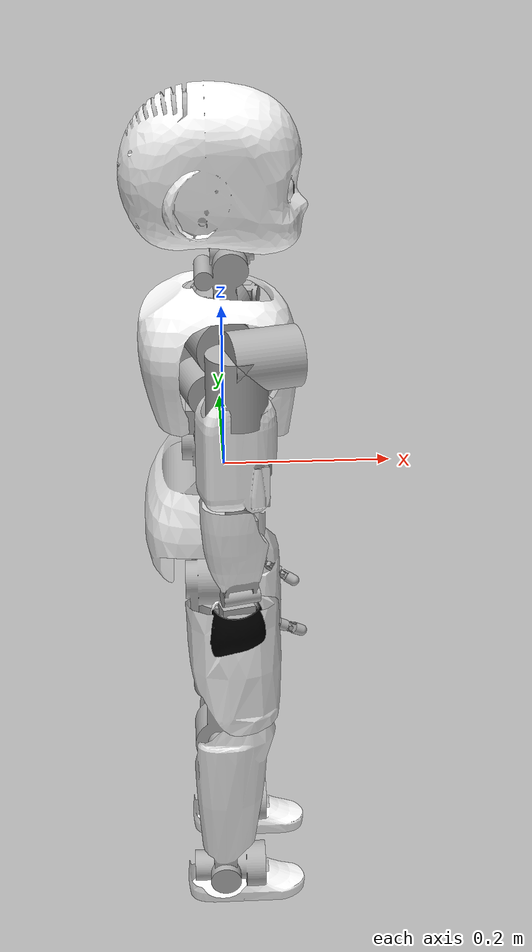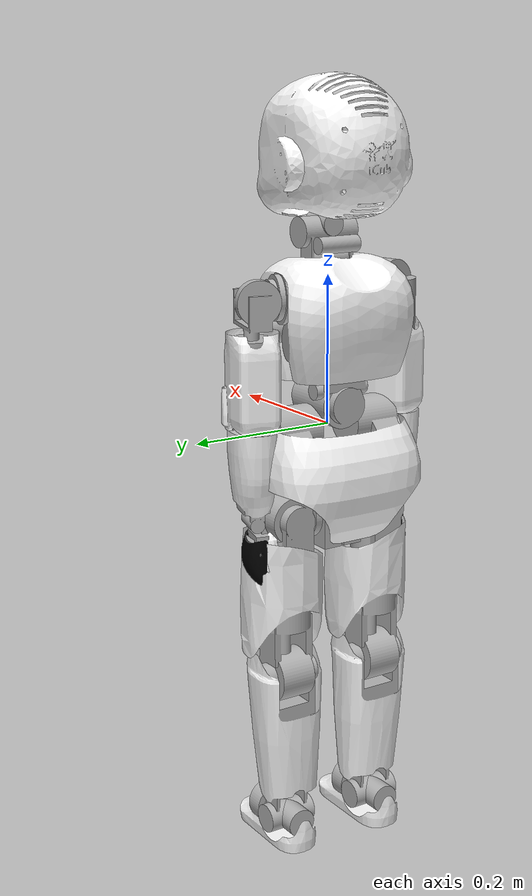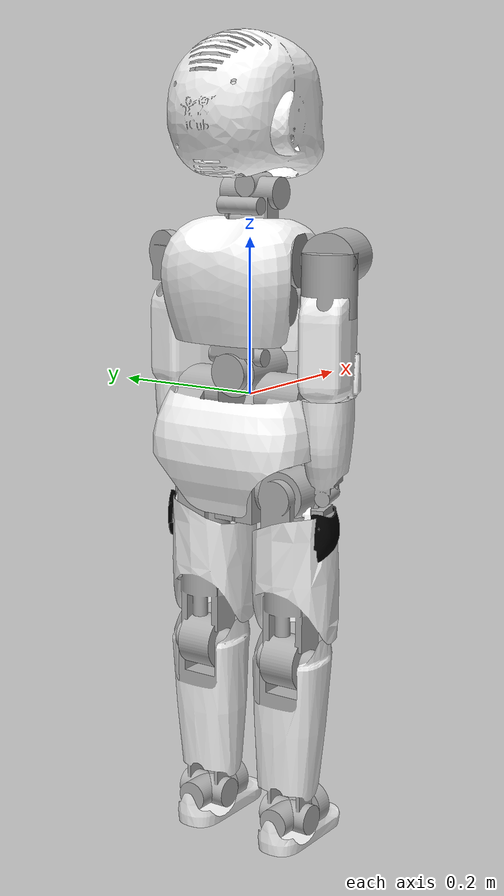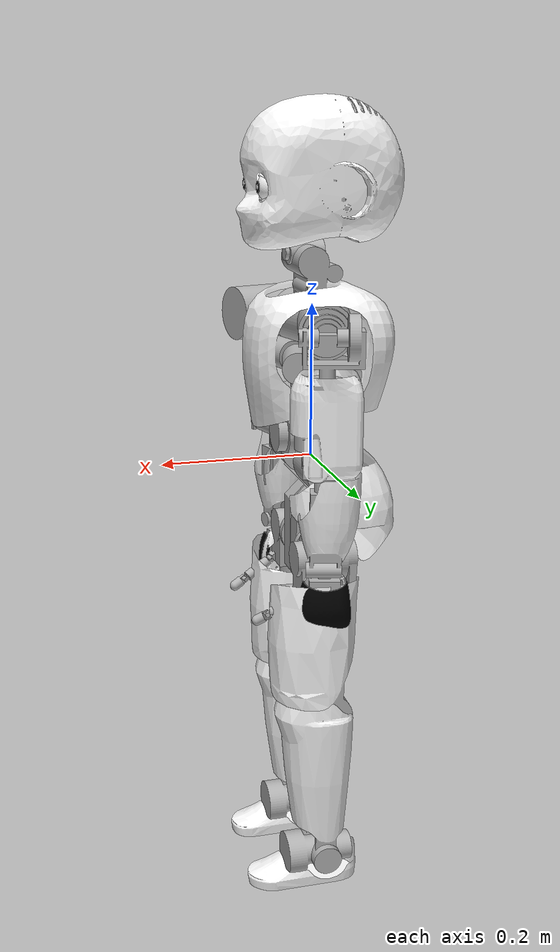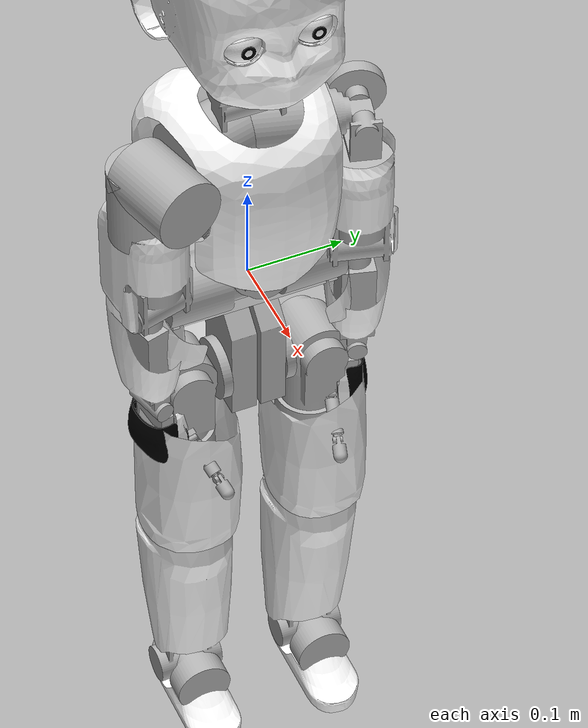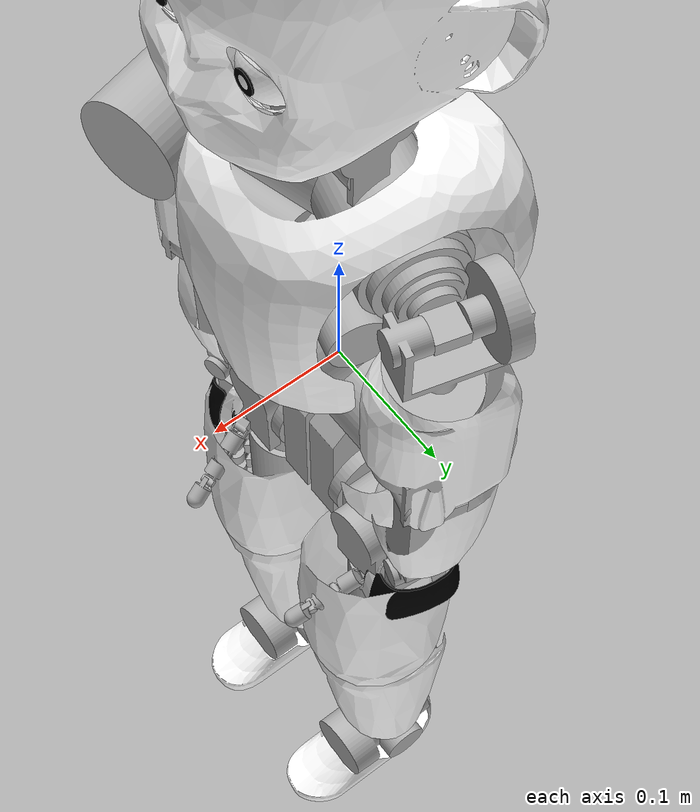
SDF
<sdf version='1.6'>
  <model name='ICub'>
    <link name='base_link'>
      <pose frame=''>0 0 0 0 -0 0</pose>
      <inertial>
        <pose frame=''>0 -0 -0.05995 0 -0 0</pose>
        <mass>0.444</mass>
        <inertia>
          <ixx>0.450625</ixx>
          <ixy>1.54074e-33</ixy>
          <ixz>-1.58819e-22</ixz>
          <iyy>0.449596</iyy>
          <iyz>-5.64219e-20</iyz>
          <izz>0.44903</izz>
        </inertia>
      </inertial>
      <visual name='base_link_fixed_joint_lump__l0_visual'>
        <pose frame=''>0 0 0 1.57079 -1.57079 3.14159</pose>
        <geometry>
          <mesh>
            <scale>1 1 1</scale>
            <uri>model://icub_with_hands/meshes/l0.dae</uri>
          </mesh>
        </geometry>
      </visual>
      <visual name='base_link_fixed_joint_lump__ll0_visual_1'>
        <pose frame=''>0 0.0681 -0.1199 -1.57079 -7e-06 3.14159</pose>
        <geometry>
          <mesh>
            <scale>1 1 1</scale>
            <uri>model://icub_with_hands/meshes/ll0.dae</uri>
          </mesh>
        </geometry>
      </visual>
      <visual name='base_link_fixed_joint_lump__rl0_visual_2'>
        <pose frame=''>0 -0.0681 -0.1199 -1.57079 -7e-06 3.14159</pose>
        <geometry>
          <mesh>
            <scale>1 1 1</scale>
            <uri>model://icub_with_hands/meshes/rl0.dae</uri>
          </mesh>
        </geometry>
      </visual>
    </link>
    <link name='l1'>
      <pose frame=''>0 0 0 1.57079 -1.57079 3.14159</pose>
      <inertial>
        <pose frame=''>0 0 0 0 -0 0</pose>
        <mass>0.111</mass>
        <inertia>
          <ixx>0.112</ixx>
          <ixy>0</ixy>
          <ixz>0</ixz>
          <iyy>0.112</iyy>
          <iyz>0</iyz>
          <izz>0.112</izz>
        </inertia>
      </inertial>
      <visual name='l1_visual'>
        <pose frame=''>0.033 0 0 1.5708 -0 0</pose>
        <geometry>
          <mesh>
            <scale>1 1 1</scale>
            <uri>model://icub_with_hands/meshes/l1.dae</uri>
          </mesh>
        </geometry>
      </visual>
    </link>
    <joint name='j1' type='revolute'>
      <child>l1</child>
      <parent>base_link</parent>
      <axis>
        <xyz>4e-06 1 0</xyz>
        <limit>
          <lower>-0.384</lower>
          <upper>1.2217</upper>
          <effort>1000</effort>
          <velocity>0.5</velocity>
        </limit>
        <dynamics>
          <spring_reference>0</spring_reference>
          <spring_stiffness>0</spring_stiffness>
        </dynamics>
        <use_parent_model_frame>1</use_parent_model_frame>
      </axis>
    </joint>
    <link name='l2'>
      <pose frame=''>-0 0 0.033 3.14159 -1.57079 3.14159</pose>
      <inertial>
        <pose frame=''>0 0 0 0 -0 0</pose>
        <mass>0.111</mass>
        <inertia>
          <ixx>0.112</ixx>
          <ixy>0</ixy>
          <ixz>0</ixz>
          <iyy>0.112</iyy>
          <iyz>0</iyz>
          <izz>0.112</izz>
        </inertia>
      </inertial>
      <visual name='l2_visual'>
        <pose frame=''>0 0 -0.0055 1.5708 0 -1.5708</pose>
        <geometry>
          <mesh>
            <scale>1 1 1</scale>
            <uri>model://icub_with_hands/meshes/l2.dae</uri>
          </mesh>
        </geometry>
      </visual>
    </link>
    <joint name='j2' type='revolute'>
      <child>l2</child>
      <parent>l1</parent>
      <axis>
        <xyz>-1 0 -4e-06</xyz>
        <limit>
          <lower>-0.5236</lower>
          <upper>0.5236</upper>
          <effort>1000</effort>
          <velocity>0.5</velocity>
        </limit>
        <dynamics>
          <spring_reference>0</spring_reference>
          <spring_stiffness>0</spring_stiffness>
        </dynamics>
        <use_parent_model_frame>1</use_parent_model_frame>
      </axis>
    </joint>
    <link name='l3'>
      <pose frame=''>0.0055 0 0.033 -3.14159 4e-06 -1.5708</pose>
      <inertial>
        <pose frame=''>0 0 0 0 -0 0</pose>
        <mass>0.111</mass>
        <inertia>
          <ixx>0.112</ixx>
          <ixy>0</ixy>
          <ixz>0</ixz>
          <iyy>0.112</iyy>
          <iyz>0</iyz>
          <izz>0.112</izz>
        </inertia>
      </inertial>
      <visual name='l3_visual'>
        <pose frame=''>0 -0.0046 -0.223 -1.5708 -0 -1.5708</pose>
        <geometry>
          <mesh>
            <scale>1 1 1</scale>
            <uri>model://icub_with_hands/meshes/l3.dae</uri>
          </mesh>
        </geometry>
      </visual>
    </link>
    <joint name='j3' type='revolute'>
      <child>l3</child>
      <parent>l2</parent>
      <axis>
        <xyz>7e-06 4e-06 -1</xyz>
        <limit>
          <lower>-0.8727</lower>
          <upper>0.8727</upper>
          <effort>1000</effort>
          <velocity>0.5</velocity>
        </limit>
        <dynamics>
          <spring_reference>0</spring_reference>
          <spring_stiffness>0</spring_stiffness>
        </dynamics>
        <use_parent_model_frame>1</use_parent_model_frame>
      </axis>
    </joint>
    <link name='l4'>
      <pose frame=''>0.010098 -1e-06 0.256 1.5708 -7e-06 4e-06</pose>
      <inertial>
        <pose frame=''>-0.016586 -0.053333 0 0 -0 0</pose>
        <mass>0.333</mass>
        <inertia>
          <ixx>0.336482</ixx>
          <ixy>-0.000147281</ixy>
          <ixz>0</ixz>
          <iyy>0.336054</iyy>
          <iyz>0</iyz>
          <izz>0.336519</izz>
        </inertia>
      </inertial>
      <visual name='l4_visual'>
        <pose frame=''>0 0.0099 0 1.5708 -0 1.5708</pose>
        <geometry>
          <mesh>
            <scale>1 1 1</scale>
            <uri>model://icub_with_hands/meshes/l4.dae</uri>
          </mesh>
        </geometry>
      </visual>
      <visual name='l4_fixed_joint_lump__la0_visual_1'>
        <pose frame=''>-0.024879 -0.08 -0.006047 3.14159 0.261793 3.14159</pose>
        <geometry>
          <mesh>
            <scale>1 1 1</scale>
            <uri>model://icub_with_hands/meshes/la0.dae</uri>
          </mesh>
        </geometry>
      </visual>
      <visual name='l4_fixed_joint_lump__ra0_visual_2'>
        <pose frame=''>-0.024879 -0.08 0.006047 -3.14159 0.2618 0</pose>
        <geometry>
          <mesh>
            <scale>1 1 1</scale>
            <uri>model://icub_with_hands/meshes/ra0.dae</uri>
          </mesh>
        </geometry>
      </visual>
    </link>
    <joint name='j4' type='revolute'>
      <child>l4</child>
      <parent>l3</parent>
      <axis>
        <xyz>4e-06 -1 0</xyz>
        <limit>
          <lower>-0.5236</lower>
          <upper>0.384</upper>
          <effort>1000</effort>
          <velocity>0.5</velocity>
        </limit>
        <dynamics>
          <spring_reference>0</spring_reference>
          <spring_stiffness>0</spring_stiffness>
        </dynamics>
        <use_parent_model_frame>1</use_parent_model_frame>
      </axis>
    </joint>
    <link name='l5'>
      <pose frame=''>0.010098 -1e-06 0.2659 6e-06 -1.57079 -3.14159</pose>
      <inertial>
        <pose frame=''>0 0 0 0 -0 0</pose>
        <mass>0.111</mass>
        <inertia>
          <ixx>0.112</ixx>
          <ixy>0</ixy>
          <ixz>0</ixz>
          <iyy>0.112</iyy>
          <iyz>0</iyz>
          <izz>0.112</izz>
        </inertia>
      </inertial>
      <visual name='l5_visual'>
        <pose frame=''>0 0 0 -1.5708 -0 -1.5708</pose>
        <geometry>
          <mesh>
            <scale>1 1 1</scale>
            <uri>model://icub_with_hands/meshes/l5.dae</uri>
          </mesh>
        </geometry>
      </visual>
    </link>
    <joint name='j5' type='revolute'>
      <child>l5</child>
      <parent>l4</parent>
      <axis>
        <xyz>1 7e-06 1.1e-05</xyz>
        <limit>
          <lower>-0.3491</lower>
          <upper>0.3491</upper>
          <effort>1000</effort>
          <velocity>0.5</velocity>
        </limit>
        <dynamics>
          <spring_reference>0</spring_reference>
          <spring_stiffness>0</spring_stiffness>
        </dynamics>
        <use_parent_model_frame>1</use_parent_model_frame>
      </axis>
    </joint>
    <link name='l6'>
      <pose frame=''>0.010098 -1e-06 0.2659 -1.5e-05 4e-06 1.5708</pose>
      <inertial>
        <pose frame=''>0 0 0 0 -0 0</pose>
        <mass>0.111</mass>
        <inertia>
          <ixx>0.112</ixx>
          <ixy>0</ixy>
          <ixz>0</ixz>
          <iyy>0.112</iyy>
          <iyz>0</iyz>
          <izz>0.112</izz>
        </inertia>
      </inertial>
      <visual name='l6_visual'>
        <pose frame=''>0 -0.0515 0.082 -1.5708 0 1.5708</pose>
        <geometry>
          <mesh>
            <scale>1 1 1</scale>
            <uri>model://icub_with_hands/meshes/l6.dae</uri>
          </mesh>
        </geometry>
      </visual>
    </link>
    <joint name='j6' type='revolute'>
      <child>l6</child>
      <parent>l5</parent>
      <axis>
        <xyz>-1.5e-05 4e-06 1</xyz>
        <limit>
          <lower>-0.8727</lower>
          <upper>0.8727</upper>
          <effort>1000</effort>
          <velocity>0.5</velocity>
        </limit>
        <dynamics>
          <spring_reference>0</spring_reference>
          <spring_stiffness>0</spring_stiffness>
        </dynamics>
        <use_parent_model_frame>1</use_parent_model_frame>
      </axis>
    </joint>
    <link name='l7'>
      <pose frame=''>0.061597 -0 0.347901 -1.5708 1.5e-05 -3.14158</pose>
      <inertial>
        <pose frame=''>0 0 0 0 -0 0</pose>
        <mass>0.111</mass>
        <inertia>
          <ixx>0.112</ixx>
          <ixy>0</ixy>
          <ixz>0</ixz>
          <iyy>0.112</iyy>
          <iyz>0</iyz>
          <izz>0.112</izz>
        </inertia>
      </inertial>
    </link>
    <joint name='j7' type='revolute'>
      <child>l7</child>
      <parent>l6</parent>
      <axis>
        <xyz>1.1e-05 -1 0</xyz>
        <limit>
          <lower>-0.5236</lower>
          <upper>0.5236</upper>
          <effort>1000</effort>
          <velocity>0.5</velocity>
        </limit>
        <dynamics>
          <spring_reference>0</spring_reference>
          <spring_stiffness>0</spring_stiffness>
        </dynamics>
        <use_parent_model_frame>1</use_parent_model_frame>
      </axis>
    </joint>
    <link name='l8'>
      <pose frame=''>0.061597 -0.034 0.347901 3.14159 1.5e-05 -3.14158</pose>
      <inertial>
        <pose frame=''>0 0 0 0 -0 0</pose>
        <mass>0.111</mass>
        <inertia>
          <ixx>0.112</ixx>
          <ixy>0</ixy>
          <ixz>0</ixz>
          <iyy>0.112</iyy>
          <iyz>0</iyz>
          <izz>0.112</izz>
        </inertia>
      </inertial>
      <visual name='l8_visual'>
        <pose frame=''>0 0 0 1.5708 0 -1.5708</pose>
        <geometry>
          <mesh>
            <scale>1 1 1</scale>
            <uri>model://icub_with_hands/meshes/l8.dae</uri>
          </mesh>
        </geometry>
      </visual>
    </link>
    <joint name='j8' type='revolute'>
      <child>l8</child>
      <parent>l7</parent>
      <axis>
        <xyz>1.5e-05 4e-06 -1</xyz>
        <limit>
          <lower>-0.5236</lower>
          <upper>0.5236</upper>
          <effort>1000</effort>
          <velocity>0.5</velocity>
        </limit>
        <dynamics>
          <spring_reference>0</spring_reference>
          <spring_stiffness>0</spring_stiffness>
        </dynamics>
        <use_parent_model_frame>1</use_parent_model_frame>
      </axis>
    </joint>
    <link name='l7s'>
      <pose frame=''>0.061597 -0 0.347901 -1.5708 1.5e-05 -3.14158</pose>
      <inertial>
        <pose frame=''>0 0 0 0 -0 0</pose>
        <mass>0.111</mass>
        <inertia>
          <ixx>0.112</ixx>
          <ixy>0</ixy>
          <ixz>0</ixz>
          <iyy>0.112</iyy>
          <iyz>0</iyz>
          <izz>0.112</izz>
        </inertia>
      </inertial>
    </link>
    <joint name='j7s' type='revolute'>
      <child>l7s</child>
      <parent>l6</parent>
      <axis>
        <xyz>1.1e-05 -1 0</xyz>
        <limit>
          <lower>-0.5236</lower>
          <upper>0.5236</upper>
          <effort>1000</effort>
          <velocity>0.5</velocity>
        </limit>
        <dynamics>
          <spring_reference>0</spring_reference>
          <spring_stiffness>0</spring_stiffness>
        </dynamics>
        <use_parent_model_frame>1</use_parent_model_frame>
      </axis>
    </joint>
    <link name='l8s'>
      <pose frame=''>0.061597 0.034 0.347901 3.14159 1.5e-05 -3.14158</pose>
      <inertial>
        <pose frame=''>0 0 0 0 -0 0</pose>
        <mass>0.111</mass>
        <inertia>
          <ixx>0.112</ixx>
          <ixy>0</ixy>
          <ixz>0</ixz>
          <iyy>0.112</iyy>
          <iyz>0</iyz>
          <izz>0.112</izz>
        </inertia>
      </inertial>
      <visual name='l8s_visual'>
        <pose frame=''>0 0 0 1.5708 0 -1.5708</pose>
        <geometry>
          <mesh>
            <scale>1 1 1</scale>
            <uri>model://icub_with_hands/meshes/l8.dae</uri>
          </mesh>
        </geometry>
      </visual>
    </link>
    <joint name='j8s' type='revolute'>
      <child>l8s</child>
      <parent>l7s</parent>
      <axis>
        <xyz>1.5e-05 4e-06 -1</xyz>
        <limit>
          <lower>-0.5236</lower>
          <upper>0.5236</upper>
          <effort>1000</effort>
          <velocity>0.5</velocity>
        </limit>
        <dynamics>
          <spring_reference>0</spring_reference>
          <spring_stiffness>0</spring_stiffness>
        </dynamics>
        <use_parent_model_frame>1</use_parent_model_frame>
      </axis>
    </joint>
    <link name='la1'>
      <pose frame=''>-0.01478 0.006046 0.176 1.57079 7e-06 2.8798</pose>
      <inertial>
        <pose frame=''>0 0 0 0 -0 0</pose>
        <mass>0.111</mass>
        <inertia>
          <ixx>0.112</ixx>
          <ixy>0</ixy>
          <ixz>0</ixz>
          <iyy>0.112</iyy>
          <iyz>0</iyz>
          <izz>0.112</izz>
        </inertia>
      </inertial>
      <visual name='la1_visual'>
        <pose frame=''>0 0 0.1077 -1.5708 0 1.5708</pose>
        <geometry>
          <mesh>
            <scale>1 1 1</scale>
            <uri>model://icub_with_hands/meshes/la1.dae</uri>
          </mesh>
        </geometry>
      </visual>
    </link>
    <joint name='laj1' type='revolute'>
      <child>la1</child>
      <parent>l4</parent>
      <axis>
        <xyz>0.258809 0.965929 2e-06</xyz>
        <limit>
          <lower>-1.6581</lower>
          <upper>0.1745</upper>
          <effort>1000</effort>
          <velocity>0.5</velocity>
        </limit>
        <dynamics>
          <spring_reference>0</spring_reference>
          <spring_stiffness>0</spring_stiffness>
        </dynamics>
        <use_parent_model_frame>1</use_parent_model_frame>
      </axis>
    </joint>
    <link name='la2'>
      <pose frame=''>0.013094 0.110077 0.176 -0.507035 -1.57079 -2.89635</pose>
      <inertial>
        <pose frame=''>0 0 0 0 -0 0</pose>
        <mass>0.111</mass>
        <inertia>
          <ixx>0.112</ixx>
          <ixy>0</ixy>
          <ixz>0</ixz>
          <iyy>0.112</iyy>
          <iyz>0</iyz>
          <izz>0.112</izz>
        </inertia>
      </inertial>
      <visual name='la2_visual'>
        <pose frame=''>0 0 0 1.5708 0 -1.5708</pose>
        <geometry>
          <mesh>
            <scale>1 1 1</scale>
            <uri>model://icub_with_hands/meshes/la2.dae</uri>
          </mesh>
        </geometry>
      </visual>
    </link>
    <joint name='laj2' type='revolute'>
      <child>la2</child>
      <parent>la1</parent>
      <axis>
        <xyz>0.965928 -0.258813 3e-06</xyz>
        <limit>
          <lower>0</lower>
          <upper>2.8065</upper>
          <effort>1000</effort>
          <velocity>0.5</velocity>
        </limit>
        <dynamics>
          <spring_reference>0</spring_reference>
          <spring_stiffness>0</spring_stiffness>
        </dynamics>
        <use_parent_model_frame>1</use_parent_model_frame>
      </axis>
    </joint>
    <link name='la3'>
      <pose frame=''>0.013094 0.110077 0.176 -3.14159 2e-06 1.309</pose>
      <inertial>
        <pose frame=''>0 0 0 0 -0 0</pose>
        <mass>0.111</mass>
        <inertia>
          <ixx>0.112</ixx>
          <ixy>0</ixy>
          <ixz>0</ixz>
          <iyy>0.112</iyy>
          <iyz>0</iyz>
          <izz>0.112</izz>
        </inertia>
      </inertial>
      <visual name='la3_visual'>
        <pose frame=''>0.0039 0.0145 0.15725 1.5708 -0 1.5708</pose>
        <geometry>
          <mesh>
            <scale>1 1 1</scale>
            <uri>model://icub_with_hands/meshes/la3.dae</uri>
          </mesh>
        </geometry>
      </visual>
    </link>
    <joint name='laj3' type='revolute'>
      <child>la3</child>
      <parent>la2</parent>
      <axis>
        <xyz>-1e-06 -2e-06 -1</xyz>
        <limit>
          <lower>-0.6458</lower>
          <upper>1.3963</upper>
          <effort>1000</effort>
          <velocity>0.5</velocity>
        </limit>
        <dynamics>
          <spring_reference>0</spring_reference>
          <spring_stiffness>0</spring_stiffness>
        </dynamics>
        <use_parent_model_frame>1</use_parent_model_frame>
      </axis>
    </joint>
    <link name='la4'>
      <pose frame=''>0.028109 0.110091 0.01875 -1.57079 0 -0.261796</pose>
      <inertial>
        <pose frame=''>0 0 0 0 -0 0</pose>
        <mass>0.111</mass>
        <inertia>
          <ixx>0.112</ixx>
          <ixy>0</ixy>
          <ixz>0</ixz>
          <iyy>0.112</iyy>
          <iyz>0</iyz>
          <izz>0.112</izz>
        </inertia>
      </inertial>
      <visual name='la4_visual'>
        <pose frame=''>-0.015 0 -0.004 1.5708 -0 0</pose>
        <geometry>
          <mesh>
            <scale>1 1 1</scale>
            <uri>model://icub_with_hands/meshes/la4.dae</uri>
          </mesh>
        </geometry>
      </visual>
    </link>
    <joint name='laj4' type='revolute'>
      <child>la4</child>
      <parent>la3</parent>
      <axis>
        <xyz>-0.258816 -0.965927 -2e-06</xyz>
        <limit>
          <lower>0.2618</lower>
          <upper>1.85</upper>
          <effort>1000</effort>
          <velocity>0.5</velocity>
        </limit>
        <dynamics>
          <spring_reference>0</spring_reference>
          <spring_stiffness>0</spring_stiffness>
        </dynamics>
        <use_parent_model_frame>1</use_parent_model_frame>
      </axis>
    </joint>
    <link name='la5'>
      <pose frame=''>0.012585 0.110109 0.01875 6e-06 0 -0.261796</pose>
      <inertial>
        <pose frame=''>0 0 0 0 -0 0</pose>
        <mass>0.111</mass>
        <inertia>
          <ixx>0.112</ixx>
          <ixy>0</ixy>
          <ixz>0</ixz>
          <iyy>0.112</iyy>
          <iyz>0</iyz>
          <izz>0.112</izz>
        </inertia>
      </inertial>
      <visual name='la5_visual'>
        <pose frame=''>0 0 -0.141 1.5708 0 -1.5708</pose>
        <geometry>
          <mesh>
            <scale>1 1 1</scale>
            <uri>model://icub_with_hands/meshes/la5.dae</uri>
          </mesh>
        </geometry>
      </visual>
    </link>
    <joint name='laj5' type='revolute'>
      <child>la5</child>
      <parent>la4</parent>
      <axis>
        <xyz>1e-06 5e-06 -1</xyz>
        <limit>
          <lower>-1.5708</lower>
          <upper>1.5708</upper>
          <effort>1000</effort>
          <velocity>0.5</velocity>
        </limit>
        <dynamics>
          <spring_reference>0</spring_reference>
          <spring_stiffness>0</spring_stiffness>
        </dynamics>
        <use_parent_model_frame>1</use_parent_model_frame>
      </axis>
    </joint>
    <link name='la6'>
      <pose frame=''>0.012585 0.11011 -0.12225 1.5708 6e-06 -1.8326</pose>
      <inertial>
        <pose frame=''>0 0 0 0 -0 0</pose>
        <mass>0.111</mass>
        <inertia>
          <ixx>0.112</ixx>
          <ixy>0</ixy>
          <ixz>0</ixz>
          <iyy>0.112</iyy>
          <iyz>0</iyz>
          <izz>0.112</izz>
        </inertia>
      </inertial>
      <visual name='la6_visual'>
        <pose frame=''>0 0 0 1.5708 -0 1.5708</pose>
        <geometry>
          <mesh>
            <scale>1 1 1</scale>
            <uri>model://icub_with_hands/meshes/la6.dae</uri>
          </mesh>
        </geometry>
      </visual>
    </link>
    <joint name='laj6' type='revolute'>
      <child>la6</child>
      <parent>la5</parent>
      <axis>
        <xyz>-0.965926 0.25882 -3e-06</xyz>
        <limit>
          <lower>-1.5708</lower>
          <upper>0</upper>
          <effort>1000</effort>
          <velocity>0.5</velocity>
        </limit>
        <dynamics>
          <spring_reference>0</spring_reference>
          <spring_stiffness>0</spring_stiffness>
        </dynamics>
        <use_parent_model_frame>1</use_parent_model_frame>
      </axis>
    </joint>
    <link name='left_palm'>
      <pose frame=''>0.012585 0.11011 -0.12225 -2.07783 -1.57079 -2.89636</pose>
      <inertial>
        <pose frame=''>-0.05649 -0.000635 0.01285 0 -0 0</pose>
        <mass>1.11</mass>
        <inertia>
          <ixx>1.12019</ixx>
          <ixy>-1.55578e-06</ixy>
          <ixz>8.84723e-05</ixz>
          <iyy>1.12042</iyy>
          <iyz>-4.91702e-06</iyz>
          <izz>1.12056</izz>
        </inertia>
      </inertial>
      <visual name='left_palm_visual'>
        <pose frame=''>-0.0625 0 0.016 0 -0 0</pose>
        <geometry>
          <mesh>
            <scale>1 1 1</scale>
            <uri>model://icub_with_hands/meshes/left_palm.dae</uri>
          </mesh>
        </geometry>
      </visual>
      <visual name='left_palm_fixed_joint_lump__lindexbase_visual_1'>
        <pose frame=''>-0.0643 -0.027 0.01225 0.0959 -0 3.06909</pose>
        <geometry>
          <mesh>
            <scale>1 1 1</scale>
            <uri>model://icub_with_hands/meshes/lindexbase.dae</uri>
          </mesh>
        </geometry>
      </visual>
      <visual name='left_palm_fixed_joint_lump__lail0_visual_2'>
        <pose frame=''>-0.075498 -0.027259 0.01225 1.6667 -0 -3.1241</pose>
        <geometry>
          <mesh>
            <scale>1 1 1</scale>
            <uri>model://icub_with_hands/meshes/lail0.dae</uri>
          </mesh>
        </geometry>
      </visual>
      <visual name='left_palm_fixed_joint_lump__llittlebase_visual_3'>
        <pose frame=''>-0.06225 0.02475 0.0135 -0.0873 0 3.1241</pose>
        <geometry>
          <mesh>
            <scale>1 1 1</scale>
            <uri>model://icub_with_hands/meshes/llittlebase.dae</uri>
          </mesh>
        </geometry>
      </visual>
      <visual name='left_palm_fixed_joint_lump__llil0_visual_4'>
        <pose frame=''>-0.077048 0.025009 0.0135 1.4835 -0 3.1241</pose>
        <geometry>
          <mesh>
            <scale>1 1 1</scale>
            <uri>model://icub_with_hands/meshes/llil0.dae</uri>
          </mesh>
        </geometry>
      </visual>
      <visual name='left_palm_fixed_joint_lump__lmiddlebase_visual_5'>
        <pose frame=''>-0.0653 -0.01 0.011 0 -0 -3.14159</pose>
        <geometry>
          <mesh>
            <scale>1 1 1</scale>
            <uri>model://icub_with_hands/meshes/lmiddlebase.dae</uri>
          </mesh>
        </geometry>
      </visual>
      <visual name='left_palm_fixed_joint_lump__lml0_visual_6'>
        <pose frame=''>-0.0803 -0.01 0.011 1.5708 -0 -3.14159</pose>
        <geometry>
          <mesh>
            <scale>1 1 1</scale>
            <uri>model://icub_with_hands/meshes/lml0.dae</uri>
          </mesh>
        </geometry>
      </visual>
      <visual name='left_palm_fixed_joint_lump__lringbase_visual_7'>
        <pose frame=''>-0.06415 0.0059 0.01175 -0.0873 -0 3.1329</pose>
        <geometry>
          <mesh>
            <scale>1 1 1</scale>
            <uri>model://icub_with_hands/meshes/lringbase.dae</uri>
          </mesh>
        </geometry>
      </visual>
      <visual name='left_palm_fixed_joint_lump__lril0_visual_8'>
        <pose frame=''>-0.078949 0.006029 0.01175 1.4835 0 3.1329</pose>
        <geometry>
          <mesh>
            <scale>1 1 1</scale>
            <uri>model://icub_with_hands/meshes/lril0.dae</uri>
          </mesh>
        </geometry>
      </visual>
    </link>
    <joint name='left_wrist_yaw' type='revolute'>
      <child>left_palm</child>
      <parent>la6</parent>
      <axis>
        <xyz>-0.258816 -0.965927 -2e-06</xyz>
        <limit>
          <lower>-0.3491</lower>
          <upper>0.6981</upper>
          <effort>1000</effort>
          <velocity>0.5</velocity>
        </limit>
        <dynamics>
          <spring_reference>0</spring_reference>
          <spring_stiffness>0</spring_stiffness>
        </dynamics>
        <use_parent_model_frame>1</use_parent_model_frame>
      </axis>
    </joint>
    <link name='lail1'>
      <pose frame=''>0.035745 0.091223 -0.197748 -3.04558 1.5533 -0.261688</pose>
      <inertial>
        <pose frame=''>0 0 0 0 -0 0</pose>
        <mass>0.111</mass>
        <inertia>
          <ixx>0.112</ixx>
          <ixy>0</ixy>
          <ixz>0</ixz>
          <iyy>0.112</iyy>
          <iyz>0</iyz>
          <izz>0.112</izz>
        </inertia>
      </inertial>
      <visual name='lail1_visual'>
        <pose frame=''>0.0259 0 0 0 -0 0</pose>
        <geometry>
          <mesh>
            <scale>1 1 1</scale>
            <uri>model://icub_with_hands/meshes/lail1.dae</uri>
          </mesh>
        </geometry>
      </visual>
    </link>
    <joint name='laij3' type='revolute'>
      <child>lail1</child>
      <parent>left_palm</parent>
      <axis>
        <xyz>-0.936557 0.350081 -0.017415</xyz>
        <limit>
          <lower>0</lower>
          <upper>1.5708</upper>
          <effort>1000</effort>
          <velocity>0.5</velocity>
        </limit>
        <dynamics>
          <spring_reference>0</spring_reference>
          <spring_stiffness>0</spring_stiffness>
        </dynamics>
        <use_parent_model_frame>1</use_parent_model_frame>
      </axis>
    </joint>
    <link name='lail2'>
      <pose frame=''>0.036183 0.091105 -0.223644 -3.04558 1.5533 -0.261688</pose>
      <inertial>
        <pose frame=''>0 0 0 0 -0 0</pose>
        <mass>0.111</mass>
        <inertia>
          <ixx>0.112</ixx>
          <ixy>0</ixy>
          <ixz>0</ixz>
          <iyy>0.112</iyy>
          <iyz>0</iyz>
          <izz>0.112</izz>
        </inertia>
      </inertial>
      <visual name='lail2_visual'>
        <pose frame=''>0.022 0 0 0 -0 0</pose>
        <geometry>
          <mesh>
            <scale>1 1 1</scale>
            <uri>model://icub_with_hands/meshes/lail2.dae</uri>
          </mesh>
        </geometry>
      </visual>
    </link>
    <joint name='laij4' type='revolute'>
      <child>lail2</child>
      <parent>lail1</parent>
      <axis>
        <xyz>-0.936557 0.350081 -0.017415</xyz>
        <limit>
          <lower>0</lower>
          <upper>1.5708</upper>
          <effort>1000</effort>
          <velocity>0.5</velocity>
        </limit>
        <dynamics>
          <spring_reference>0</spring_reference>
          <spring_stiffness>0</spring_stiffness>
        </dynamics>
        <use_parent_model_frame>1</use_parent_model_frame>
      </axis>
    </joint>
    <link name='lail3'>
      <pose frame=''>0.036555 0.091006 -0.24564 -3.04558 1.5533 -0.261688</pose>
      <inertial>
        <pose frame=''>0 0 0 0 -0 0</pose>
        <mass>0.111</mass>
        <inertia>
          <ixx>0.112</ixx>
          <ixy>0</ixy>
          <ixz>0</ixz>
          <iyy>0.112</iyy>
          <iyz>0</iyz>
          <izz>0.112</izz>
        </inertia>
      </inertial>
      <visual name='lail3_visual'>
        <pose frame=''>0.0168 0 0 -1.5708 0 0</pose>
        <geometry>
          <mesh>
            <scale>1 1 1</scale>
            <uri>model://icub_with_hands/meshes/lail3.dae</uri>
          </mesh>
        </geometry>
      </visual>
    </link>
    <joint name='laij5' type='revolute'>
      <child>lail3</child>
      <parent>lail2</parent>
      <axis>
        <xyz>-0.936557 0.350081 -0.017415</xyz>
        <limit>
          <lower>0</lower>
          <upper>1.5708</upper>
          <effort>1000</effort>
          <velocity>0.5</velocity>
        </limit>
        <dynamics>
          <spring_reference>0</spring_reference>
          <spring_stiffness>0</spring_stiffness>
        </dynamics>
        <use_parent_model_frame>1</use_parent_model_frame>
      </axis>
    </joint>
    <link name='llil1'>
      <pose frame=''>-0.015065 0.103543 -0.199298 -0.087405 1.55331 2.87969</pose>
      <inertial>
        <pose frame=''>0 0 0 0 -0 0</pose>
        <mass>0.111</mass>
        <inertia>
          <ixx>0.112</ixx>
          <ixy>0</ixy>
          <ixz>0</ixz>
          <iyy>0.112</iyy>
          <iyz>0</iyz>
          <izz>0.112</izz>
        </inertia>
      </inertial>
      <visual name='llil1_visual'>
        <pose frame=''>0.0218 0 0 0 -0 0</pose>
        <geometry>
          <mesh>
            <scale>1 1 1</scale>
            <uri>model://icub_with_hands/meshes/llil1.dae</uri>
          </mesh>
        </geometry>
      </visual>
    </link>
    <joint name='llij3' type='revolute'>
      <child>llil1</child>
      <parent>left_palm</parent>
      <axis>
        <xyz>-0.984666 0.173576 0.017422</xyz>
        <limit>
          <lower>0</lower>
          <upper>1.5708</upper>
          <effort>1000</effort>
          <velocity>0.5</velocity>
        </limit>
        <dynamics>
          <spring_reference>0</spring_reference>
          <spring_stiffness>0</spring_stiffness>
        </dynamics>
        <use_parent_model_frame>1</use_parent_model_frame>
      </axis>
    </joint>
    <link name='llil2'>
      <pose frame=''>-0.015434 0.103642 -0.221094 -0.087405 1.55331 2.87969</pose>
      <inertial>
        <pose frame=''>0 0 0 0 -0 0</pose>
        <mass>0.111</mass>
        <inertia>
          <ixx>0.112</ixx>
          <ixy>0</ixy>
          <ixz>0</ixz>
          <iyy>0.112</iyy>
          <iyz>0</iyz>
          <izz>0.112</izz>
        </inertia>
      </inertial>
      <visual name='llil2_visual'>
        <pose frame=''>0.019 0 0 0 -0 0</pose>
        <geometry>
          <mesh>
            <scale>1 1 1</scale>
            <uri>model://icub_with_hands/meshes/llil2.dae</uri>
          </mesh>
        </geometry>
      </visual>
    </link>
    <joint name='llij4' type='revolute'>
      <child>llil2</child>
      <parent>llil1</parent>
      <axis>
        <xyz>-0.984666 0.173576 0.017422</xyz>
        <limit>
          <lower>0</lower>
          <upper>1.5708</upper>
          <effort>1000</effort>
          <velocity>0.5</velocity>
        </limit>
        <dynamics>
          <spring_reference>0</spring_reference>
          <spring_stiffness>0</spring_stiffness>
        </dynamics>
        <use_parent_model_frame>1</use_parent_model_frame>
      </axis>
    </joint>
    <link name='llil3'>
      <pose frame=''>-0.015755 0.103728 -0.240092 -0.087405 1.55331 2.87969</pose>
      <inertial>
        <pose frame=''>0 0 0 0 -0 0</pose>
        <mass>0.111</mass>
        <inertia>
          <ixx>0.112</ixx>
          <ixy>0</ixy>
          <ixz>0</ixz>
          <iyy>0.112</iyy>
          <iyz>0</iyz>
          <izz>0.112</izz>
        </inertia>
      </inertial>
      <visual name='llil3_visual'>
        <pose frame=''>0.0168 0 0 -1.5708 0 0</pose>
        <geometry>
          <mesh>
            <scale>1 1 1</scale>
            <uri>model://icub_with_hands/meshes/llil3.dae</uri>
          </mesh>
        </geometry>
      </visual>
    </link>
    <joint name='llij5' type='revolute'>
      <child>llil3</child>
      <parent>llil2</parent>
      <axis>
        <xyz>-0.984666 0.173576 0.017422</xyz>
        <limit>
          <lower>0</lower>
          <upper>1.5708</upper>
          <effort>1000</effort>
          <velocity>0.5</velocity>
        </limit>
        <dynamics>
          <spring_reference>0</spring_reference>
          <spring_stiffness>0</spring_stiffness>
        </dynamics>
        <use_parent_model_frame>1</use_parent_model_frame>
      </axis>
    </joint>
    <link name='lml1'>
      <pose frame=''>0.019398 0.096897 -0.20255 -2.96684 1.57079 -0.087047</pose>
      <inertial>
        <pose frame=''>0 0 0 0 -0 0</pose>
        <mass>0.111</mass>
        <inertia>
          <ixx>0.112</ixx>
          <ixy>0</ixy>
          <ixz>0</ixz>
          <iyy>0.112</iyy>
          <iyz>0</iyz>
          <izz>0.112</izz>
        </inertia>
      </inertial>
      <visual name='lml1_visual'>
        <pose frame=''>0.0285 0 0 0 -0 0</pose>
        <geometry>
          <mesh>
            <scale>1 1 1</scale>
            <uri>model://icub_with_hands/meshes/lml1.dae</uri>
          </mesh>
        </geometry>
      </visual>
    </link>
    <joint name='lmj3' type='revolute'>
      <child>lml1</child>
      <parent>left_palm</parent>
      <axis>
        <xyz>-0.965926 0.25882 -1.1e-05</xyz>
        <limit>
          <lower>0</lower>
          <upper>1.5708</upper>
          <effort>1000</effort>
          <velocity>0.5</velocity>
        </limit>
        <dynamics>
          <spring_reference>0</spring_reference>
          <spring_stiffness>0</spring_stiffness>
        </dynamics>
        <use_parent_model_frame>1</use_parent_model_frame>
      </axis>
    </joint>
    <link name='lml2'>
      <pose frame=''>0.019398 0.096897 -0.23105 -2.96684 1.57079 -0.087047</pose>
      <inertial>
        <pose frame=''>0 0 0 0 -0 0</pose>
        <mass>0.111</mass>
        <inertia>
          <ixx>0.112</ixx>
          <ixy>0</ixy>
          <ixz>0</ixz>
          <iyy>0.112</iyy>
          <iyz>0</iyz>
          <izz>0.112</izz>
        </inertia>
      </inertial>
      <visual name='lml2_visual'>
        <pose frame=''>0.024 0 0 0 -0 0</pose>
        <geometry>
          <mesh>
            <scale>1 1 1</scale>
            <uri>model://icub_with_hands/meshes/lml2.dae</uri>
          </mesh>
        </geometry>
      </visual>
    </link>
    <joint name='lmj4' type='revolute'>
      <child>lml2</child>
      <parent>lml1</parent>
      <axis>
        <xyz>-0.965926 0.25882 -1.1e-05</xyz>
        <limit>
          <lower>0</lower>
          <upper>1.5708</upper>
          <effort>1000</effort>
          <velocity>0.5</velocity>
        </limit>
        <dynamics>
          <spring_reference>0</spring_reference>
          <spring_stiffness>0</spring_stiffness>
        </dynamics>
        <use_parent_model_frame>1</use_parent_model_frame>
      </axis>
    </joint>
    <link name='lml3'>
      <pose frame=''>0.019398 0.096897 -0.25505 -2.96684 1.57079 -0.087047</pose>
      <inertial>
        <pose frame=''>0 0 0 0 -0 0</pose>
        <mass>0.111</mass>
        <inertia>
          <ixx>0.112</ixx>
          <ixy>0</ixy>
          <ixz>0</ixz>
          <iyy>0.112</iyy>
          <iyz>0</iyz>
          <izz>0.112</izz>
        </inertia>
      </inertial>
      <visual name='lml3_visual'>
        <pose frame=''>0.0168 0 0 -1.5708 0 0</pose>
        <geometry>
          <mesh>
            <scale>1 1 1</scale>
            <uri>model://icub_with_hands/meshes/lml3.dae</uri>
          </mesh>
        </geometry>
      </visual>
    </link>
    <joint name='lmj5' type='revolute'>
      <child>lml3</child>
      <parent>lml2</parent>
      <axis>
        <xyz>-0.965926 0.25882 -1.1e-05</xyz>
        <limit>
          <lower>0</lower>
          <upper>1.5708</upper>
          <effort>1000</effort>
          <velocity>0.5</velocity>
        </limit>
        <dynamics>
          <spring_reference>0</spring_reference>
          <spring_stiffness>0</spring_stiffness>
        </dynamics>
        <use_parent_model_frame>1</use_parent_model_frame>
      </axis>
    </joint>
    <link name='lril1'>
      <pose frame=''>0.003721 0.100321 -0.201199 -0.087515 1.56211 2.87958</pose>
      <inertial>
        <pose frame=''>0 0 0 0 -0 0</pose>
        <mass>0.111</mass>
        <inertia>
          <ixx>0.112</ixx>
          <ixy>0</ixy>
          <ixz>0</ixz>
          <iyy>0.112</iyy>
          <iyz>0</iyz>
          <izz>0.112</izz>
        </inertia>
      </inertial>
      <visual name='lril1_visual'>
        <pose frame=''>0.0259 0 0 0 -0 0</pose>
        <geometry>
          <mesh>
            <scale>1 1 1</scale>
            <uri>model://icub_with_hands/meshes/lril1.dae</uri>
          </mesh>
        </geometry>
      </visual>
    </link>
    <joint name='lrij3' type='revolute'>
      <child>lril1</child>
      <parent>left_palm</parent>
      <axis>
        <xyz>-0.984777 0.173606 0.008656</xyz>
        <limit>
          <lower>0</lower>
          <upper>1.5708</upper>
          <effort>1000</effort>
          <velocity>0.5</velocity>
        </limit>
        <dynamics>
          <spring_reference>0</spring_reference>
          <spring_stiffness>0</spring_stiffness>
        </dynamics>
        <use_parent_model_frame>1</use_parent_model_frame>
      </axis>
    </joint>
    <link name='lril2'>
      <pose frame=''>0.003504 0.100379 -0.227098 -0.087515 1.56211 2.87958</pose>
      <inertial>
        <pose frame=''>0 0 0 0 -0 0</pose>
        <mass>0.111</mass>
        <inertia>
          <ixx>0.112</ixx>
          <ixy>0</ixy>
          <ixz>0</ixz>
          <iyy>0.112</iyy>
          <iyz>0</iyz>
          <izz>0.112</izz>
        </inertia>
      </inertial>
      <visual name='lril2_visual'>
        <pose frame=''>0.022 0 0 0 -0 0</pose>
        <geometry>
          <mesh>
            <scale>1 1 1</scale>
            <uri>model://icub_with_hands/meshes/lril2.dae</uri>
          </mesh>
        </geometry>
      </visual>
    </link>
    <joint name='lrij4' type='revolute'>
      <child>lril2</child>
      <parent>lril1</parent>
      <axis>
        <xyz>-0.984777 0.173606 0.008656</xyz>
        <limit>
          <lower>0</lower>
          <upper>1.5708</upper>
          <effort>1000</effort>
          <velocity>0.5</velocity>
        </limit>
        <dynamics>
          <spring_reference>0</spring_reference>
          <spring_stiffness>0</spring_stiffness>
        </dynamics>
        <use_parent_model_frame>1</use_parent_model_frame>
      </axis>
    </joint>
    <link name='lril3'>
      <pose frame=''>0.003319 0.100429 -0.249098 -0.087515 1.56211 2.87958</pose>
      <inertial>
        <pose frame=''>0 0 0 0 -0 0</pose>
        <mass>0.111</mass>
        <inertia>
          <ixx>0.112</ixx>
          <ixy>0</ixy>
          <ixz>0</ixz>
          <iyy>0.112</iyy>
          <iyz>0</iyz>
          <izz>0.112</izz>
        </inertia>
      </inertial>
      <visual name='lril3_visual'>
        <pose frame=''>0.0168 0 0 -1.5708 0 0</pose>
        <geometry>
          <mesh>
            <scale>1 1 1</scale>
            <uri>model://icub_with_hands/meshes/lril3.dae</uri>
          </mesh>
        </geometry>
      </visual>
    </link>
    <joint name='lrij5' type='revolute'>
      <child>lril3</child>
      <parent>lril2</parent>
      <axis>
        <xyz>-0.984777 0.173606 0.008656</xyz>
        <limit>
          <lower>0</lower>
          <upper>1.5708</upper>
          <effort>1000</effort>
          <velocity>0.5</velocity>
        </limit>
        <dynamics>
          <spring_reference>0</spring_reference>
          <spring_stiffness>0</spring_stiffness>
        </dynamics>
        <use_parent_model_frame>1</use_parent_model_frame>
      </axis>
    </joint>
    <link name='ltl0'>
      <pose frame=''>0.019079 0.086629 -0.16085 0.078598 0.4975 -0.261795</pose>
      <inertial>
        <pose frame=''>0 0 0 0 -0 0</pose>
        <mass>0.222</mass>
        <inertia>
          <ixx>0.224</ixx>
          <ixy>0</ixy>
          <ixz>0</ixz>
          <iyy>0.224</iyy>
          <iyz>5.29396e-23</iyz>
          <izz>0.224</izz>
        </inertia>
      </inertial>
      <visual name='ltl0_visual'>
        <pose frame=''>0 0 0 -1.5708 0 0</pose>
        <geometry>
          <mesh>
            <scale>1 1 1</scale>
            <uri>model://icub_with_hands/meshes/ltl0.dae</uri>
          </mesh>
        </geometry>
      </visual>
      <visual name='ltl0_fixed_joint_lump__ltl1_visual_1'>
        <pose frame=''>0.021 -0.0056 0 -1.5708 0 0</pose>
        <geometry>
          <mesh>
            <scale>1 1 1</scale>
            <uri>model://icub_with_hands/meshes/ltl1.dae</uri>
          </mesh>
        </geometry>
      </visual>
    </link>
    <joint name='ltj2' type='revolute'>
      <child>ltl0</child>
      <parent>left_palm</parent>
      <axis>
        <xyz>-0.439225 0.198975 -0.876065</xyz>
        <limit>
          <lower>0</lower>
          <upper>1.5708</upper>
          <effort>1000</effort>
          <velocity>0.5</velocity>
        </limit>
        <dynamics>
          <spring_reference>0</spring_reference>
          <spring_stiffness>0</spring_stiffness>
        </dynamics>
        <use_parent_model_frame>1</use_parent_model_frame>
      </axis>
    </joint>
    <link name='ltl2'>
      <pose frame=''>0.035257 0.076515 -0.171258 -1.4922 0.4975 -0.261795</pose>
      <inertial>
        <pose frame=''>0 0 0 0 -0 0</pose>
        <mass>0.111</mass>
        <inertia>
          <ixx>0.112</ixx>
          <ixy>0</ixy>
          <ixz>0</ixz>
          <iyy>0.112</iyy>
          <iyz>0</iyz>
          <izz>0.112</izz>
        </inertia>
      </inertial>
      <visual name='ltl2_visual'>
        <pose frame=''>0.026 0 0 0 -0 0</pose>
        <geometry>
          <mesh>
            <scale>1 1 1</scale>
            <uri>model://icub_with_hands/meshes/ltl2.dae</uri>
          </mesh>
        </geometry>
      </visual>
    </link>
    <joint name='ltj4' type='revolute'>
      <child>ltl2</child>
      <parent>ltl0</parent>
      <axis>
        <xyz>0.294209 0.953247 0.068996</xyz>
        <limit>
          <lower>0</lower>
          <upper>1.5708</upper>
          <effort>1000</effort>
          <velocity>0.5</velocity>
        </limit>
        <dynamics>
          <spring_reference>0</spring_reference>
          <spring_stiffness>0</spring_stiffness>
        </dynamics>
        <use_parent_model_frame>1</use_parent_model_frame>
      </axis>
    </joint>
    <link name='ltl3'>
      <pose frame=''>0.057327 0.070602 -0.183666 -1.4922 0.4975 -0.261795</pose>
      <inertial>
        <pose frame=''>0 0 0 0 -0 0</pose>
        <mass>0.111</mass>
        <inertia>
          <ixx>0.112</ixx>
          <ixy>0</ixy>
          <ixz>0</ixz>
          <iyy>0.112</iyy>
          <iyz>0</iyz>
          <izz>0.112</izz>
        </inertia>
      </inertial>
      <visual name='ltl3_visual'>
        <pose frame=''>0.022 0 0 0 -0 0</pose>
        <geometry>
          <mesh>
            <scale>1 1 1</scale>
            <uri>model://icub_with_hands/meshes/ltl3.dae</uri>
          </mesh>
        </geometry>
      </visual>
    </link>
    <joint name='ltj5' type='revolute'>
      <child>ltl3</child>
      <parent>ltl2</parent>
      <axis>
        <xyz>0.294209 0.953247 0.068996</xyz>
        <limit>
          <lower>0</lower>
          <upper>1.5708</upper>
          <effort>1000</effort>
          <velocity>0.5</velocity>
        </limit>
        <dynamics>
          <spring_reference>0</spring_reference>
          <spring_stiffness>0</spring_stiffness>
        </dynamics>
        <use_parent_model_frame>1</use_parent_model_frame>
      </axis>
    </joint>
    <link name='ltl4'>
      <pose frame=''>0.076001 0.065598 -0.194165 -1.4922 0.4975 -0.261795</pose>
      <inertial>
        <pose frame=''>0 0 0 0 -0 0</pose>
        <mass>0.111</mass>
        <inertia>
          <ixx>0.112</ixx>
          <ixy>0</ixy>
          <ixz>0</ixz>
          <iyy>0.112</iyy>
          <iyz>0</iyz>
          <izz>0.112</izz>
        </inertia>
      </inertial>
      <visual name='ltl4_visual'>
        <pose frame=''>0.0168 0 0 0 -0 0</pose>
        <geometry>
          <mesh>
            <scale>1 1 1</scale>
            <uri>model://icub_with_hands/meshes/ltl4.dae</uri>
          </mesh>
        </geometry>
      </visual>
    </link>
    <joint name='ltj6' type='revolute'>
      <child>ltl4</child>
      <parent>ltl3</parent>
      <axis>
        <xyz>0.294209 0.953247 0.068996</xyz>
        <limit>
          <lower>0</lower>
          <upper>1.5708</upper>
          <effort>1000</effort>
          <velocity>0.5</velocity>
        </limit>
        <dynamics>
          <spring_reference>0</spring_reference>
          <spring_stiffness>0</spring_stiffness>
        </dynamics>
        <use_parent_model_frame>1</use_parent_model_frame>
      </axis>
    </joint>
    <link name='ra1'>
      <pose frame=''>-0.01478 -0.006048 0.176 -1.57079 -7e-06 0.261804</pose>
      <inertial>
        <pose frame=''>0 0 0 0 -0 0</pose>
        <mass>0.111</mass>
        <inertia>
          <ixx>0.112</ixx>
          <ixy>0</ixy>
          <ixz>0</ixz>
          <iyy>0.112</iyy>
          <iyz>0</iyz>
          <izz>0.112</izz>
        </inertia>
      </inertial>
      <visual name='ra1_visual'>
        <pose frame=''>0 0 -0.1077 1.5708 0 -1.5708</pose>
        <geometry>
          <mesh>
            <scale>1 1 1</scale>
            <uri>model://icub_with_hands/meshes/ra1.dae</uri>
          </mesh>
        </geometry>
      </visual>
    </link>
    <joint name='raj1' type='revolute'>
      <child>ra1</child>
      <parent>l4</parent>
      <axis>
        <xyz>-0.258823 0.965925 5e-06</xyz>
        <limit>
          <lower>-1.6581</lower>
          <upper>0.1745</upper>
          <effort>1000</effort>
          <velocity>0.5</velocity>
        </limit>
        <dynamics>
          <spring_reference>0</spring_reference>
          <spring_stiffness>0</spring_stiffness>
        </dynamics>
        <use_parent_model_frame>1</use_parent_model_frame>
      </axis>
    </joint>
    <link name='ra2'>
      <pose frame=''>0.013096 -0.110078 0.175999 2.67348 -1.57078 -2.41167</pose>
      <inertial>
        <pose frame=''>0 0 0 0 -0 0</pose>
        <mass>0.111</mass>
        <inertia>
          <ixx>0.112</ixx>
          <ixy>0</ixy>
          <ixz>0</ixz>
          <iyy>0.112</iyy>
          <iyz>0</iyz>
          <izz>0.112</izz>
        </inertia>
      </inertial>
      <visual name='ra2_visual'>
        <pose frame=''>0 0 0 -1.5708 -0 -1.5708</pose>
        <geometry>
          <mesh>
            <scale>1 1 1</scale>
            <uri>model://icub_with_hands/meshes/ra2.dae</uri>
          </mesh>
        </geometry>
      </visual>
    </link>
    <joint name='raj2' type='revolute'>
      <child>ra2</child>
      <parent>ra1</parent>
      <axis>
        <xyz>-0.965924 -0.258827 -1.1e-05</xyz>
        <limit>
          <lower>0</lower>
          <upper>2.8065</upper>
          <effort>1000</effort>
          <velocity>0.5</velocity>
        </limit>
        <dynamics>
          <spring_reference>0</spring_reference>
          <spring_stiffness>0</spring_stiffness>
        </dynamics>
        <use_parent_model_frame>1</use_parent_model_frame>
      </axis>
    </joint>
    <link name='ra3'>
      <pose frame=''>0.013096 -0.110078 0.175999 7e-06 9e-06 -1.30899</pose>
      <inertial>
        <pose frame=''>0 0 0 0 -0 0</pose>
        <mass>0.111</mass>
        <inertia>
          <ixx>0.112</ixx>
          <ixy>0</ixy>
          <ixz>0</ixz>
          <iyy>0.112</iyy>
          <iyz>0</iyz>
          <izz>0.112</izz>
        </inertia>
      </inertial>
      <visual name='ra3_visual'>
        <pose frame=''>0.0039 0.0145 -0.15725 -1.5708 -0 -1.5708</pose>
        <geometry>
          <mesh>
            <scale>1 1 1</scale>
            <uri>model://icub_with_hands/meshes/ra3.dae</uri>
          </mesh>
        </geometry>
      </visual>
    </link>
    <joint name='raj3' type='revolute'>
      <child>ra3</child>
      <parent>ra2</parent>
      <axis>
        <xyz>-4e-06 -1.1e-05 1</xyz>
        <limit>
          <lower>-0.6458</lower>
          <upper>1.3963</upper>
          <effort>1000</effort>
          <velocity>0.5</velocity>
        </limit>
        <dynamics>
          <spring_reference>0</spring_reference>
          <spring_stiffness>0</spring_stiffness>
        </dynamics>
        <use_parent_model_frame>1</use_parent_model_frame>
      </axis>
    </joint>
    <link name='ra4'>
      <pose frame=''>0.028112 -0.110091 0.018749 -1.57081 7e-06 -2.87979</pose>
      <inertial>
        <pose frame=''>0 0 0 0 -0 0</pose>
        <mass>0.111</mass>
        <inertia>
          <ixx>0.112</ixx>
          <ixy>0</ixy>
          <ixz>0</ixz>
          <iyy>0.112</iyy>
          <iyz>0</iyz>
          <izz>0.112</izz>
        </inertia>
      </inertial>
      <visual name='ra4_visual'>
        <pose frame=''>0.015 0 -0.004 1.5708 -0 0</pose>
        <geometry>
          <mesh>
            <scale>1 1 1</scale>
            <uri>model://icub_with_hands/meshes/ra4.dae</uri>
          </mesh>
        </geometry>
      </visual>
    </link>
    <joint name='raj4' type='revolute'>
      <child>ra4</child>
      <parent>ra3</parent>
      <axis>
        <xyz>0.258823 -0.965925 -1.3e-05</xyz>
        <limit>
          <lower>0.2618</lower>
          <upper>1.85</upper>
          <effort>1000</effort>
          <velocity>0.5</velocity>
        </limit>
        <dynamics>
          <spring_reference>0</spring_reference>
          <spring_stiffness>0</spring_stiffness>
        </dynamics>
        <use_parent_model_frame>1</use_parent_model_frame>
      </axis>
    </joint>
    <link name='ra5'>
      <pose frame=''>0.012587 -0.110109 0.018749 -9e-06 7e-06 -2.87979</pose>
      <inertial>
        <pose frame=''>0 0 0 0 -0 0</pose>
        <mass>0.111</mass>
        <inertia>
          <ixx>0.112</ixx>
          <ixy>0</ixy>
          <ixz>0</ixz>
          <iyy>0.112</iyy>
          <iyz>0</iyz>
          <izz>0.112</izz>
        </inertia>
      </inertial>
      <visual name='ra5_visual'>
        <pose frame=''>0 0 -0.141 1.5708 0 -1.5708</pose>
        <geometry>
          <mesh>
            <scale>1 1 1</scale>
            <uri>model://icub_with_hands/meshes/ra5.dae</uri>
          </mesh>
        </geometry>
      </visual>
    </link>
    <joint name='raj5' type='revolute'>
      <child>ra5</child>
      <parent>ra4</parent>
      <axis>
        <xyz>-4e-06 -1.1e-05 1</xyz>
        <limit>
          <lower>-1.5708</lower>
          <upper>1.5708</upper>
          <effort>1000</effort>
          <velocity>0.5</velocity>
        </limit>
        <dynamics>
          <spring_reference>0</spring_reference>
          <spring_stiffness>0</spring_stiffness>
        </dynamics>
        <use_parent_model_frame>1</use_parent_model_frame>
      </axis>
    </joint>
    <link name='ra6'>
      <pose frame=''>0.012588 -0.110108 -0.122251 1.57079 -9e-06 1.8326</pose>
      <inertial>
        <pose frame=''>0 0 0 0 -0 0</pose>
        <mass>0.111</mass>
        <inertia>
          <ixx>0.112</ixx>
          <ixy>0</ixy>
          <ixz>0</ixz>
          <iyy>0.112</iyy>
          <iyz>0</iyz>
          <izz>0.112</izz>
        </inertia>
      </inertial>
      <visual name='ra6_visual'>
        <pose frame=''>0 0 0 1.5708 -0 1.5708</pose>
        <geometry>
          <mesh>
            <scale>1 1 1</scale>
            <uri>model://icub_with_hands/meshes/ra6.dae</uri>
          </mesh>
        </geometry>
      </visual>
    </link>
    <joint name='raj6' type='revolute'>
      <child>ra6</child>
      <parent>ra5</parent>
      <axis>
        <xyz>0.965926 0.25882 3e-06</xyz>
        <limit>
          <lower>-1.5708</lower>
          <upper>0</upper>
          <effort>1000</effort>
          <velocity>0.5</velocity>
        </limit>
        <dynamics>
          <spring_reference>0</spring_reference>
          <spring_stiffness>0</spring_stiffness>
        </dynamics>
        <use_parent_model_frame>1</use_parent_model_frame>
      </axis>
    </joint>
    <link name='right_palm'>
      <pose frame=''>0.012588 -0.110108 -0.122251 0.261467 -1.57078 -1.57046</pose>
      <inertial>
        <pose frame=''>-0.05685 0.000635 0.01285 0 -0 0</pose>
        <mass>1.11</mass>
        <inertia>
          <ixx>1.12019</ixx>
          <ixy>1.20924e-05</ixy>
          <ixz>8.82325e-05</ixz>
          <iyy>1.12042</iyy>
          <iyz>4.91702e-06</iyz>
          <izz>1.12056</izz>
        </inertia>
      </inertial>
      <visual name='right_palm_visual'>
        <pose frame=''>-0.0625 0 0.016 0 -0 -3.14159</pose>
        <geometry>
          <mesh>
            <scale>1 1 1</scale>
            <uri>model://icub_with_hands/meshes/right_palm.dae</uri>
          </mesh>
        </geometry>
      </visual>
      <visual name='right_palm_fixed_joint_lump__indexbase_visual_1'>
        <pose frame=''>-0.0643 0.027 0.01225 0.0959 -0 -3.12409</pose>
        <geometry>
          <mesh>
            <scale>1 1 1</scale>
            <uri>model://icub_with_hands/meshes/indexbase.dae</uri>
          </mesh>
        </geometry>
      </visual>
      <visual name='right_palm_fixed_joint_lump__il0_visual_2'>
        <pose frame=''>-0.079098 0.026741 0.01225 1.6667 0 -3.12409</pose>
        <geometry>
          <mesh>
            <scale>1 1 1</scale>
            <uri>model://icub_with_hands/meshes/il0.dae</uri>
          </mesh>
        </geometry>
      </visual>
      <visual name='right_palm_fixed_joint_lump__littlebase_visual_3'>
        <pose frame=''>-0.06225 -0.02475 0.0135 0.0873 -0 -3.12409</pose>
        <geometry>
          <mesh>
            <scale>1 1 1</scale>
            <uri>model://icub_with_hands/meshes/littlebase.dae</uri>
          </mesh>
        </geometry>
      </visual>
      <visual name='right_palm_fixed_joint_lump__lil0_visual_4'>
        <pose frame=''>-0.077048 -0.025009 0.0135 1.6581 -0 -3.12409</pose>
        <geometry>
          <mesh>
            <scale>1 1 1</scale>
            <uri>model://icub_with_hands/meshes/lil0.dae</uri>
          </mesh>
        </geometry>
      </visual>
      <visual name='right_palm_fixed_joint_lump__middlebase_visual_5'>
        <pose frame=''>-0.0653 0.01 0.011 0 -0 -3.14159</pose>
        <geometry>
          <mesh>
            <scale>1 1 1</scale>
            <uri>model://icub_with_hands/meshes/middlebase.dae</uri>
          </mesh>
        </geometry>
      </visual>
      <visual name='right_palm_fixed_joint_lump__ml0_visual_6'>
        <pose frame=''>-0.0803 0.01 0.011 1.5708 -0 -3.14159</pose>
        <geometry>
          <mesh>
            <scale>1 1 1</scale>
            <uri>model://icub_with_hands/meshes/ml0.dae</uri>
          </mesh>
        </geometry>
      </visual>
      <visual name='right_palm_fixed_joint_lump__ringbase_visual_7'>
        <pose frame=''>-0.06415 -0.0059 0.01175 0.0873 -0 -3.13289</pose>
        <geometry>
          <mesh>
            <scale>1 1 1</scale>
            <uri>model://icub_with_hands/meshes/ringbase.dae</uri>
          </mesh>
        </geometry>
      </visual>
      <visual name='right_palm_fixed_joint_lump__ril0_visual_8'>
        <pose frame=''>-0.078949 -0.006029 0.01175 1.6581 0 -3.13289</pose>
        <geometry>
          <mesh>
            <scale>1 1 1</scale>
            <uri>model://icub_with_hands/meshes/ril0.dae</uri>
          </mesh>
        </geometry>
      </visual>
    </link>
    <joint name='right_wrist_yaw' type='revolute'>
      <child>right_palm</child>
      <parent>ra6</parent>
      <axis>
        <xyz>-0.258823 0.965925 1.3e-05</xyz>
        <limit>
          <lower>-0.3491</lower>
          <upper>0.6981</upper>
          <effort>1000</effort>
          <velocity>0.5</velocity>
        </limit>
        <dynamics>
          <spring_reference>0</spring_reference>
          <spring_stiffness>0</spring_stiffness>
        </dynamics>
        <use_parent_model_frame>1</use_parent_model_frame>
      </axis>
    </joint>
    <link name='il1'>
      <pose frame=''>0.035247 -0.091353 -0.201348 -3.04642 1.55329 -2.88052</pose>
      <inertial>
        <pose frame=''>0 0 0 0 -0 0</pose>
        <mass>0.111</mass>
        <inertia>
          <ixx>0.112</ixx>
          <ixy>0</ixy>
          <ixz>0</ixz>
          <iyy>0.112</iyy>
          <iyz>0</iyz>
          <izz>0.112</izz>
        </inertia>
      </inertial>
      <visual name='il1_visual'>
        <pose frame=''>0.0259 0 0 0 -0 0</pose>
        <geometry>
          <mesh>
            <scale>1 1 1</scale>
            <uri>model://icub_with_hands/meshes/il1.dae</uri>
          </mesh>
        </geometry>
      </visual>
    </link>
    <joint name='ij3' type='revolute'>
      <child>il1</child>
      <parent>right_palm</parent>
      <axis>
        <xyz>0.986123 0.165101 -0.017424</xyz>
        <limit>
          <lower>0</lower>
          <upper>1.5708</upper>
          <effort>1000</effort>
          <velocity>0.5</velocity>
        </limit>
        <dynamics>
          <spring_reference>0</spring_reference>
          <spring_stiffness>0</spring_stiffness>
        </dynamics>
        <use_parent_model_frame>1</use_parent_model_frame>
      </axis>
    </joint>
    <link name='il2'>
      <pose frame=''>0.034809 -0.09147 -0.227244 -3.04642 1.55329 -2.88052</pose>
      <inertial>
        <pose frame=''>0 0 0 0 -0 0</pose>
        <mass>0.111</mass>
        <inertia>
          <ixx>0.112</ixx>
          <ixy>0</ixy>
          <ixz>0</ixz>
          <iyy>0.112</iyy>
          <iyz>0</iyz>
          <izz>0.112</izz>
        </inertia>
      </inertial>
      <visual name='il2_visual'>
        <pose frame=''>0.022 0 0 0 -0 0</pose>
        <geometry>
          <mesh>
            <scale>1 1 1</scale>
            <uri>model://icub_with_hands/meshes/il2.dae</uri>
          </mesh>
        </geometry>
      </visual>
    </link>
    <joint name='ij4' type='revolute'>
      <child>il2</child>
      <parent>il1</parent>
      <axis>
        <xyz>0.986123 0.165101 -0.017424</xyz>
        <limit>
          <lower>0</lower>
          <upper>1.5708</upper>
          <effort>1000</effort>
          <velocity>0.5</velocity>
        </limit>
        <dynamics>
          <spring_reference>0</spring_reference>
          <spring_stiffness>0</spring_stiffness>
        </dynamics>
        <use_parent_model_frame>1</use_parent_model_frame>
      </axis>
    </joint>
    <link name='il3'>
      <pose frame=''>0.034437 -0.091569 -0.249241 -3.04642 1.55329 -2.88052</pose>
      <inertial>
        <pose frame=''>0 0 0 0 -0 0</pose>
        <mass>0.111</mass>
        <inertia>
          <ixx>0.112</ixx>
          <ixy>0</ixy>
          <ixz>0</ixz>
          <iyy>0.112</iyy>
          <iyz>0</iyz>
          <izz>0.112</izz>
        </inertia>
      </inertial>
      <visual name='il3_visual'>
        <pose frame=''>0.0168 0 0 -1.5708 0 0</pose>
        <geometry>
          <mesh>
            <scale>1 1 1</scale>
            <uri>model://icub_with_hands/meshes/il3.dae</uri>
          </mesh>
        </geometry>
      </visual>
    </link>
    <joint name='ij5' type='revolute'>
      <child>il3</child>
      <parent>il2</parent>
      <axis>
        <xyz>0.986123 0.165101 -0.017424</xyz>
        <limit>
          <lower>0</lower>
          <upper>1.5708</upper>
          <effort>1000</effort>
          <velocity>0.5</velocity>
        </limit>
        <dynamics>
          <spring_reference>0</spring_reference>
          <spring_stiffness>0</spring_stiffness>
        </dynamics>
        <use_parent_model_frame>1</use_parent_model_frame>
      </axis>
    </joint>
    <link name='lil1'>
      <pose frame=''>-0.015063 -0.10354 -0.199298 -3.05502 1.55329 -2.88052</pose>
      <inertial>
        <pose frame=''>0 0 0 0 -0 0</pose>
        <mass>0.111</mass>
        <inertia>
          <ixx>0.112</ixx>
          <ixy>0</ixy>
          <ixz>0</ixz>
          <iyy>0.112</iyy>
          <iyz>0</iyz>
          <izz>0.112</izz>
        </inertia>
      </inertial>
      <visual name='lil1_visual'>
        <pose frame=''>0.0218 0 0 0 -0 0</pose>
        <geometry>
          <mesh>
            <scale>1 1 1</scale>
            <uri>model://icub_with_hands/meshes/lil1.dae</uri>
          </mesh>
        </geometry>
      </visual>
    </link>
    <joint name='lij3' type='revolute'>
      <child>lil1</child>
      <parent>right_palm</parent>
      <axis>
        <xyz>0.984666 0.173576 -0.017438</xyz>
        <limit>
          <lower>0</lower>
          <upper>1.5708</upper>
          <effort>1000</effort>
          <velocity>0.5</velocity>
        </limit>
        <dynamics>
          <spring_reference>0</spring_reference>
          <spring_stiffness>0</spring_stiffness>
        </dynamics>
        <use_parent_model_frame>1</use_parent_model_frame>
      </axis>
    </joint>
    <link name='lil2'>
      <pose frame=''>-0.015432 -0.103638 -0.221095 -3.05502 1.55329 -2.88052</pose>
      <inertial>
        <pose frame=''>0 0 0 0 -0 0</pose>
        <mass>0.111</mass>
        <inertia>
          <ixx>0.112</ixx>
          <ixy>0</ixy>
          <ixz>0</ixz>
          <iyy>0.112</iyy>
          <iyz>0</iyz>
          <izz>0.112</izz>
        </inertia>
      </inertial>
      <visual name='lil2_visual'>
        <pose frame=''>0.019 0 0 0 -0 0</pose>
        <geometry>
          <mesh>
            <scale>1 1 1</scale>
            <uri>model://icub_with_hands/meshes/lil2.dae</uri>
          </mesh>
        </geometry>
      </visual>
    </link>
    <joint name='lij4' type='revolute'>
      <child>lil2</child>
      <parent>lil1</parent>
      <axis>
        <xyz>0.984666 0.173576 -0.017438</xyz>
        <limit>
          <lower>0</lower>
          <upper>1.5708</upper>
          <effort>1000</effort>
          <velocity>0.5</velocity>
        </limit>
        <dynamics>
          <spring_reference>0</spring_reference>
          <spring_stiffness>0</spring_stiffness>
        </dynamics>
        <use_parent_model_frame>1</use_parent_model_frame>
      </axis>
    </joint>
    <link name='lil3'>
      <pose frame=''>-0.015753 -0.103724 -0.240092 -3.05502 1.55329 -2.88052</pose>
      <inertial>
        <pose frame=''>0 0 0 0 -0 0</pose>
        <mass>0.111</mass>
        <inertia>
          <ixx>0.112</ixx>
          <ixy>0</ixy>
          <ixz>0</ixz>
          <iyy>0.112</iyy>
          <iyz>0</iyz>
          <izz>0.112</izz>
        </inertia>
      </inertial>
      <visual name='lil3_visual'>
        <pose frame=''>0.0168 0 0 -1.5708 0 0</pose>
        <geometry>
          <mesh>
            <scale>1 1 1</scale>
            <uri>model://icub_with_hands/meshes/lil3.dae</uri>
          </mesh>
        </geometry>
      </visual>
    </link>
    <joint name='lij5' type='revolute'>
      <child>lil3</child>
      <parent>lil2</parent>
      <axis>
        <xyz>0.984666 0.173576 -0.017438</xyz>
        <limit>
          <lower>0</lower>
          <upper>1.5708</upper>
          <effort>1000</effort>
          <velocity>0.5</velocity>
        </limit>
        <dynamics>
          <spring_reference>0</spring_reference>
          <spring_stiffness>0</spring_stiffness>
        </dynamics>
        <use_parent_model_frame>1</use_parent_model_frame>
      </axis>
    </joint>
    <link name='ml1'>
      <pose frame=''>0.0194 -0.096893 -0.202551 1.86842 1.57078 2.13022</pose>
      <inertial>
        <pose frame=''>0 0 0 0 -0 0</pose>
        <mass>0.111</mass>
        <inertia>
          <ixx>0.112</ixx>
          <ixy>0</ixy>
          <ixz>0</ixz>
          <iyy>0.112</iyy>
          <iyz>0</iyz>
          <izz>0.112</izz>
        </inertia>
      </inertial>
      <visual name='ml1_visual'>
        <pose frame=''>0.0285 0 0 0 -0 0</pose>
        <geometry>
          <mesh>
            <scale>1 1 1</scale>
            <uri>model://icub_with_hands/meshes/ml1.dae</uri>
          </mesh>
        </geometry>
      </visual>
    </link>
    <joint name='mj3' type='revolute'>
      <child>ml1</child>
      <parent>right_palm</parent>
      <axis>
        <xyz>0.965926 0.25882 -4e-06</xyz>
        <limit>
          <lower>0</lower>
          <upper>1.5708</upper>
          <effort>1000</effort>
          <velocity>0.5</velocity>
        </limit>
        <dynamics>
          <spring_reference>0</spring_reference>
          <spring_stiffness>0</spring_stiffness>
        </dynamics>
        <use_parent_model_frame>1</use_parent_model_frame>
      </axis>
    </joint>
    <link name='ml2'>
      <pose frame=''>0.0194 -0.096893 -0.231051 1.86842 1.57078 2.13022</pose>
      <inertial>
        <pose frame=''>0 0 0 0 -0 0</pose>
        <mass>0.111</mass>
        <inertia>
          <ixx>0.112</ixx>
          <ixy>0</ixy>
          <ixz>0</ixz>
          <iyy>0.112</iyy>
          <iyz>0</iyz>
          <izz>0.112</izz>
        </inertia>
      </inertial>
      <visual name='ml2_visual'>
        <pose frame=''>0.024 0 0 0 -0 0</pose>
        <geometry>
          <mesh>
            <scale>1 1 1</scale>
            <uri>model://icub_with_hands/meshes/ml2.dae</uri>
          </mesh>
        </geometry>
      </visual>
    </link>
    <joint name='mj4' type='revolute'>
      <child>ml2</child>
      <parent>ml1</parent>
      <axis>
        <xyz>0.965926 0.25882 -4e-06</xyz>
        <limit>
          <lower>0</lower>
          <upper>1.5708</upper>
          <effort>1000</effort>
          <velocity>0.5</velocity>
        </limit>
        <dynamics>
          <spring_reference>0</spring_reference>
          <spring_stiffness>0</spring_stiffness>
        </dynamics>
        <use_parent_model_frame>1</use_parent_model_frame>
      </axis>
    </joint>
    <link name='ml3'>
      <pose frame=''>0.0194 -0.096893 -0.255051 1.86842 1.57078 2.13022</pose>
      <inertial>
        <pose frame=''>0 0 0 0 -0 0</pose>
        <mass>0.111</mass>
        <inertia>
          <ixx>0.112</ixx>
          <ixy>0</ixy>
          <ixz>0</ixz>
          <iyy>0.112</iyy>
          <iyz>0</iyz>
          <izz>0.112</izz>
        </inertia>
      </inertial>
      <visual name='ml3_visual'>
        <pose frame=''>0.0168 0 0 -1.5708 0 0</pose>
        <geometry>
          <mesh>
            <scale>1 1 1</scale>
            <uri>model://icub_with_hands/meshes/ml3.dae</uri>
          </mesh>
        </geometry>
      </visual>
    </link>
    <joint name='mj5' type='revolute'>
      <child>ml3</child>
      <parent>ml2</parent>
      <axis>
        <xyz>0.965926 0.25882 -4e-06</xyz>
        <limit>
          <lower>0</lower>
          <upper>1.5708</upper>
          <effort>1000</effort>
          <velocity>0.5</velocity>
        </limit>
        <dynamics>
          <spring_reference>0</spring_reference>
          <spring_stiffness>0</spring_stiffness>
        </dynamics>
        <use_parent_model_frame>1</use_parent_model_frame>
      </axis>
    </joint>
    <link name='ril1'>
      <pose frame=''>0.003723 -0.100318 -0.2012 -3.05576 1.56209 -2.88126</pose>
      <inertial>
        <pose frame=''>0 0 0 0 -0 0</pose>
        <mass>0.111</mass>
        <inertia>
          <ixx>0.112</ixx>
          <ixy>0</ixy>
          <ixz>0</ixz>
          <iyy>0.112</iyy>
          <iyz>0</iyz>
          <izz>0.112</izz>
        </inertia>
      </inertial>
      <visual name='ril1_visual'>
        <pose frame=''>0.0259 0 0 0 -0 0</pose>
        <geometry>
          <mesh>
            <scale>1 1 1</scale>
            <uri>model://icub_with_hands/meshes/ril1.dae</uri>
          </mesh>
        </geometry>
      </visual>
    </link>
    <joint name='rij3' type='revolute'>
      <child>ril1</child>
      <parent>right_palm</parent>
      <axis>
        <xyz>0.984777 0.173606 -0.008672</xyz>
        <limit>
          <lower>0</lower>
          <upper>1.5708</upper>
          <effort>1000</effort>
          <velocity>0.5</velocity>
        </limit>
        <dynamics>
          <spring_reference>0</spring_reference>
          <spring_stiffness>0</spring_stiffness>
        </dynamics>
        <use_parent_model_frame>1</use_parent_model_frame>
      </axis>
    </joint>
    <link name='ril2'>
      <pose frame=''>0.003506 -0.100376 -0.227099 -3.05576 1.56209 -2.88126</pose>
      <inertial>
        <pose frame=''>0 0 0 0 -0 0</pose>
        <mass>0.111</mass>
        <inertia>
          <ixx>0.112</ixx>
          <ixy>0</ixy>
          <ixz>0</ixz>
          <iyy>0.112</iyy>
          <iyz>0</iyz>
          <izz>0.112</izz>
        </inertia>
      </inertial>
      <visual name='ril2_visual'>
        <pose frame=''>0.022 0 0 0 -0 0</pose>
        <geometry>
          <mesh>
            <scale>1 1 1</scale>
            <uri>model://icub_with_hands/meshes/ril2.dae</uri>
          </mesh>
        </geometry>
      </visual>
    </link>
    <joint name='rij4' type='revolute'>
      <child>ril2</child>
      <parent>ril1</parent>
      <axis>
        <xyz>0.984777 0.173606 -0.008672</xyz>
        <limit>
          <lower>0</lower>
          <upper>1.5708</upper>
          <effort>1000</effort>
          <velocity>0.5</velocity>
        </limit>
        <dynamics>
          <spring_reference>0</spring_reference>
          <spring_stiffness>0</spring_stiffness>
        </dynamics>
        <use_parent_model_frame>1</use_parent_model_frame>
      </axis>
    </joint>
    <link name='ril3'>
      <pose frame=''>0.003321 -0.100425 -0.249098 -3.05576 1.56209 -2.88126</pose>
      <inertial>
        <pose frame=''>0 0 0 0 -0 0</pose>
        <mass>0.111</mass>
        <inertia>
          <ixx>0.112</ixx>
          <ixy>0</ixy>
          <ixz>0</ixz>
          <iyy>0.112</iyy>
          <iyz>0</iyz>
          <izz>0.112</izz>
        </inertia>
      </inertial>
      <visual name='ril3_visual'>
        <pose frame=''>0.0168 0 0 -1.5708 0 0</pose>
        <geometry>
          <mesh>
            <scale>1 1 1</scale>
            <uri>model://icub_with_hands/meshes/ril3.dae</uri>
          </mesh>
        </geometry>
      </visual>
    </link>
    <joint name='rij5' type='revolute'>
      <child>ril3</child>
      <parent>ril2</parent>
      <axis>
        <xyz>0.984777 0.173606 -0.008672</xyz>
        <limit>
          <lower>0</lower>
          <upper>1.5708</upper>
          <effort>1000</effort>
          <velocity>0.5</velocity>
        </limit>
        <dynamics>
          <spring_reference>0</spring_reference>
          <spring_stiffness>0</spring_stiffness>
        </dynamics>
        <use_parent_model_frame>1</use_parent_model_frame>
      </axis>
    </joint>
    <link name='tl0'>
      <pose frame=''>0.019082 -0.086626 -0.16085 -0.078582 0.4975 0.261811</pose>
      <inertial>
        <pose frame=''>0 0 0 0 -0 0</pose>
        <mass>0.222</mass>
        <inertia>
          <ixx>0.224</ixx>
          <ixy>0</ixy>
          <ixz>0</ixz>
          <iyy>0.224</iyy>
          <iyz>5.29396e-23</iyz>
          <izz>0.224</izz>
        </inertia>
      </inertial>
      <visual name='tl0_visual'>
        <pose frame=''>0 0 0 -1.5708 0 0</pose>
        <geometry>
          <mesh>
            <scale>1 1 1</scale>
            <uri>model://icub_with_hands/meshes/tl0.dae</uri>
          </mesh>
        </geometry>
      </visual>
      <visual name='tl0_fixed_joint_lump__tl1_visual_1'>
        <pose frame=''>0.021 0.0056 -0 -1.5708 0 0</pose>
        <geometry>
          <mesh>
            <scale>1 1 1</scale>
            <uri>model://icub_with_hands/meshes/tl1.dae</uri>
          </mesh>
        </geometry>
      </visual>
    </link>
    <joint name='tj2' type='revolute'>
      <child>tl0</child>
      <parent>right_palm</parent>
      <axis>
        <xyz>0.439227 0.198966 0.876066</xyz>
        <limit>
          <lower>0</lower>
          <upper>1.5708</upper>
          <effort>1000</effort>
          <velocity>0.5</velocity>
        </limit>
        <dynamics>
          <spring_reference>0</spring_reference>
          <spring_stiffness>0</spring_stiffness>
        </dynamics>
        <use_parent_model_frame>1</use_parent_model_frame>
      </axis>
    </joint>
    <link name='tl2'>
      <pose frame=''>0.03526 -0.076512 -0.171259 -1.64938 0.4975 0.261811</pose>
      <inertial>
        <pose frame=''>0 0 0 0 -0 0</pose>
        <mass>0.111</mass>
        <inertia>
          <ixx>0.112</ixx>
          <ixy>0</ixy>
          <ixz>0</ixz>
          <iyy>0.112</iyy>
          <iyz>0</iyz>
          <izz>0.112</izz>
        </inertia>
      </inertial>
      <visual name='tl2_visual'>
        <pose frame=''>0.026 0 0 0 -0 0</pose>
        <geometry>
          <mesh>
            <scale>1 1 1</scale>
            <uri>model://icub_with_hands/meshes/tl2.dae</uri>
          </mesh>
        </geometry>
      </visual>
    </link>
    <joint name='tj4' type='revolute'>
      <child>tl2</child>
      <parent>tl0</parent>
      <axis>
        <xyz>-0.294219 0.953245 -0.068988</xyz>
        <limit>
          <lower>0</lower>
          <upper>1.5708</upper>
          <effort>1000</effort>
          <velocity>0.5</velocity>
        </limit>
        <dynamics>
          <spring_reference>0</spring_reference>
          <spring_stiffness>0</spring_stiffness>
        </dynamics>
        <use_parent_model_frame>1</use_parent_model_frame>
      </axis>
    </joint>
    <link name='tl3'>
      <pose frame=''>0.05733 -0.070598 -0.183667 -1.64938 0.4975 0.261811</pose>
      <inertial>
        <pose frame=''>0 0 0 0 -0 0</pose>
        <mass>0.111</mass>
        <inertia>
          <ixx>0.112</ixx>
          <ixy>0</ixy>
          <ixz>0</ixz>
          <iyy>0.112</iyy>
          <iyz>0</iyz>
          <izz>0.112</izz>
        </inertia>
      </inertial>
      <visual name='tl3_visual'>
        <pose frame=''>0.022 0 0 0 -0 0</pose>
        <geometry>
          <mesh>
            <scale>1 1 1</scale>
            <uri>model://icub_with_hands/meshes/tl3.dae</uri>
          </mesh>
        </geometry>
      </visual>
    </link>
    <joint name='tj5' type='revolute'>
      <child>tl3</child>
      <parent>tl2</parent>
      <axis>
        <xyz>-0.294219 0.953245 -0.068988</xyz>
        <limit>
          <lower>0</lower>
          <upper>1.5708</upper>
          <effort>1000</effort>
          <velocity>0.5</velocity>
        </limit>
        <dynamics>
          <spring_reference>0</spring_reference>
          <spring_stiffness>0</spring_stiffness>
        </dynamics>
        <use_parent_model_frame>1</use_parent_model_frame>
      </axis>
    </joint>
    <link name='tl4'>
      <pose frame=''>0.076004 -0.065594 -0.194166 -1.64938 0.4975 0.261811</pose>
      <inertial>
        <pose frame=''>0 0 0 0 -0 0</pose>
        <mass>0.111</mass>
        <inertia>
          <ixx>0.112</ixx>
          <ixy>0</ixy>
          <ixz>0</ixz>
          <iyy>0.112</iyy>
          <iyz>0</iyz>
          <izz>0.112</izz>
        </inertia>
      </inertial>
      <visual name='tl4_visual'>
        <pose frame=''>0.0168 0 0 0 -0 0</pose>
        <geometry>
          <mesh>
            <scale>1 1 1</scale>
            <uri>model://icub_with_hands/meshes/tl4.dae</uri>
          </mesh>
        </geometry>
      </visual>
    </link>
    <joint name='tj6' type='revolute'>
      <child>tl4</child>
      <parent>tl3</parent>
      <axis>
        <xyz>-0.294219 0.953245 -0.068988</xyz>
        <limit>
          <lower>0</lower>
          <upper>1.5708</upper>
          <effort>1000</effort>
          <velocity>0.5</velocity>
        </limit>
        <dynamics>
          <spring_reference>0</spring_reference>
          <spring_stiffness>0</spring_stiffness>
        </dynamics>
        <use_parent_model_frame>1</use_parent_model_frame>
      </axis>
    </joint>
    <link name='ll1'>
      <pose frame=''>0 0.0681 -0.1199 -1.57079 -7e-06 3.14159</pose>
      <inertial>
        <pose frame=''>0 0 0 0 -0 0</pose>
        <mass>0.111</mass>
        <inertia>
          <ixx>0.112</ixx>
          <ixy>0</ixy>
          <ixz>0</ixz>
          <iyy>0.112</iyy>
          <iyz>0</iyz>
          <izz>0.112</izz>
        </inertia>
      </inertial>
      <visual name='ll1_visual'>
        <pose frame=''>0 0 0 -1.5708 0 1.5708</pose>
        <geometry>
          <mesh>
            <scale>1 1 1</scale>
            <uri>model://icub_with_hands/meshes/ll1.dae</uri>
          </mesh>
        </geometry>
      </visual>
    </link>
    <joint name='llaj1' type='revolute'>
      <child>ll1</child>
      <parent>base_link</parent>
      <axis>
        <xyz>0 -1 4e-06</xyz>
        <limit>
          <lower>-0.5236</lower>
          <upper>1.5708</upper>
          <effort>1000</effort>
          <velocity>0.5</velocity>
        </limit>
        <dynamics>
          <spring_reference>0</spring_reference>
          <spring_stiffness>0</spring_stiffness>
        </dynamics>
        <use_parent_model_frame>1</use_parent_model_frame>
      </axis>
    </joint>
    <link name='ll2'>
      <pose frame=''>0 0.0681 -0.1199 -2.3562 1.57079 -2.35619</pose>
      <inertial>
        <pose frame=''>0 0 0 0 -0 0</pose>
        <mass>0.111</mass>
        <inertia>
          <ixx>0.112</ixx>
          <ixy>0</ixy>
          <ixz>0</ixz>
          <iyy>0.112</iyy>
          <iyz>0</iyz>
          <izz>0.112</izz>
        </inertia>
      </inertial>
      <visual name='ll2_visual'>
        <pose frame=''>0 0 0 1.5708 0 -1.5708</pose>
        <geometry>
          <mesh>
            <scale>1 1 1</scale>
            <uri>model://icub_with_hands/meshes/ll2.dae</uri>
          </mesh>
        </geometry>
      </visual>
    </link>
    <joint name='llaj2' type='revolute'>
      <child>ll2</child>
      <parent>ll1</parent>
      <axis>
        <xyz>1 4e-06 -4e-06</xyz>
        <limit>
          <lower>0</lower>
          <upper>1.5708</upper>
          <effort>1000</effort>
          <velocity>0.5</velocity>
        </limit>
        <dynamics>
          <spring_reference>0</spring_reference>
          <spring_stiffness>0</spring_stiffness>
        </dynamics>
        <use_parent_model_frame>1</use_parent_model_frame>
      </axis>
    </joint>
    <link name='ll3'>
      <pose frame=''>0 0.0681 -0.1199 -0 -7e-06 -1.57079</pose>
      <inertial>
        <pose frame=''>0 0 0 0 -0 0</pose>
        <mass>0.111</mass>
        <inertia>
          <ixx>0.112</ixx>
          <ixy>0</ixy>
          <ixz>0</ixz>
          <iyy>0.112</iyy>
          <iyz>0</iyz>
          <izz>0.112</izz>
        </inertia>
      </inertial>
      <visual name='ll3_visual'>
        <pose frame=''>0 0 -0.225 1.5708 -0 1.5708</pose>
        <geometry>
          <mesh>
            <scale>1 1 1</scale>
            <uri>model://icub_with_hands/meshes/ll3.dae</uri>
          </mesh>
        </geometry>
      </visual>
    </link>
    <joint name='llaj3' type='revolute'>
      <child>ll3</child>
      <parent>ll2</parent>
      <axis>
        <xyz>-0 7e-06 1</xyz>
        <limit>
          <lower>-1.3963</lower>
          <upper>1.3614</upper>
          <effort>1000</effort>
          <velocity>0.5</velocity>
        </limit>
        <dynamics>
          <spring_reference>0</spring_reference>
          <spring_stiffness>0</spring_stiffness>
        </dynamics>
        <use_parent_model_frame>1</use_parent_model_frame>
      </axis>
    </joint>
    <link name='ll4'>
      <pose frame=''>0 0.068098 -0.3449 1.57079 0 7e-06</pose>
      <inertial>
        <pose frame=''>0 0 0 0 -0 0</pose>
        <mass>0.111</mass>
        <inertia>
          <ixx>0.112</ixx>
          <ixy>0</ixy>
          <ixz>0</ixz>
          <iyy>0.112</iyy>
          <iyz>0</iyz>
          <izz>0.112</izz>
        </inertia>
      </inertial>
      <visual name='ll4_visual'>
        <pose frame=''>0 -0.215 0 -3.14159 -0 1.5708</pose>
        <geometry>
          <mesh>
            <scale>1 1 1</scale>
            <uri>model://icub_with_hands/meshes/ll4.dae</uri>
          </mesh>
        </geometry>
      </visual>
    </link>
    <joint name='llaj4' type='revolute'>
      <child>ll4</child>
      <parent>ll3</parent>
      <axis>
        <xyz>7e-06 -1 4e-06</xyz>
        <limit>
          <lower>-2.0944</lower>
          <upper>0</upper>
          <effort>1000</effort>
          <velocity>0.5</velocity>
        </limit>
        <dynamics>
          <spring_reference>0</spring_reference>
          <spring_stiffness>0</spring_stiffness>
        </dynamics>
        <use_parent_model_frame>1</use_parent_model_frame>
      </axis>
    </joint>
    <link name='ll5'>
      <pose frame=''>0 0.068098 -0.5599 2.35621 -1.57079 2.3562</pose>
      <inertial>
        <pose frame=''>0 0 0 0 -0 0</pose>
        <mass>0.111</mass>
        <inertia>
          <ixx>0.112</ixx>
          <ixy>0</ixy>
          <ixz>0</ixz>
          <iyy>0.112</iyy>
          <iyz>0</iyz>
          <izz>0.112</izz>
        </inertia>
      </inertial>
      <visual name='ll5_visual'>
        <pose frame=''>0 0 0 -1.5708 0 0</pose>
        <geometry>
          <mesh>
            <scale>1 1 1</scale>
            <uri>model://icub_with_hands/meshes/ll5.dae</uri>
          </mesh>
        </geometry>
      </visual>
    </link>
    <joint name='llaj5' type='revolute'>
      <child>ll5</child>
      <parent>ll4</parent>
      <axis>
        <xyz>-1.5e-05 1 -4e-06</xyz>
        <limit>
          <lower>-0.3491</lower>
          <upper>0.6807</upper>
          <effort>1000</effort>
          <velocity>0.5</velocity>
        </limit>
        <dynamics>
          <spring_reference>0</spring_reference>
          <spring_stiffness>0</spring_stiffness>
        </dynamics>
        <use_parent_model_frame>1</use_parent_model_frame>
      </axis>
    </joint>
    <link name='ll6'>
      <pose frame=''>0 0.068098 -0.5599 0.785406 -1.57079 2.3562</pose>
      <inertial>
        <pose frame=''>0 0 0 0 -0 0</pose>
        <mass>0.111</mass>
        <inertia>
          <ixx>0.112</ixx>
          <ixy>0</ixy>
          <ixz>0</ixz>
          <iyy>0.112</iyy>
          <iyz>0</iyz>
          <izz>0.112</izz>
        </inertia>
      </inertial>
      <visual name='ll6_visual'>
        <pose frame=''>-0.041 0 0 0 -0 0</pose>
        <geometry>
          <mesh>
            <scale>1 1 1</scale>
            <uri>model://icub_with_hands/meshes/ll6.dae</uri>
          </mesh>
        </geometry>
      </visual>
    </link>
    <joint name='llaj6' type='revolute'>
      <child>ll6</child>
      <parent>ll5</parent>
      <axis>
        <xyz>1 1.1e-05 4e-06</xyz>
        <limit>
          <lower>-0.384</lower>
          <upper>0.384</upper>
          <effort>1000</effort>
          <velocity>0.5</velocity>
        </limit>
        <dynamics>
          <spring_reference>0</spring_reference>
          <spring_stiffness>0</spring_stiffness>
        </dynamics>
        <use_parent_model_frame>1</use_parent_model_frame>
      </axis>
    </joint>
    <link name='rl1'>
      <pose frame=''>0 -0.0681 -0.1199 -1.57079 -7e-06 3.14159</pose>
      <inertial>
        <pose frame=''>0 0 0 0 -0 0</pose>
        <mass>0.111</mass>
        <inertia>
          <ixx>0.112</ixx>
          <ixy>0</ixy>
          <ixz>0</ixz>
          <iyy>0.112</iyy>
          <iyz>0</iyz>
          <izz>0.112</izz>
        </inertia>
      </inertial>
      <visual name='rl1_visual'>
        <pose frame=''>0 0 0 1.5708 -0 1.5708</pose>
        <geometry>
          <mesh>
            <scale>1 1 1</scale>
            <uri>model://icub_with_hands/meshes/rl1.dae</uri>
          </mesh>
        </geometry>
      </visual>
    </link>
    <joint name='rlaj1' type='revolute'>
      <child>rl1</child>
      <parent>base_link</parent>
      <axis>
        <xyz>0 -1 4e-06</xyz>
        <limit>
          <lower>-0.5236</lower>
          <upper>1.5708</upper>
          <effort>1000</effort>
          <velocity>0.5</velocity>
        </limit>
        <dynamics>
          <spring_reference>0</spring_reference>
          <spring_stiffness>0</spring_stiffness>
        </dynamics>
        <use_parent_model_frame>1</use_parent_model_frame>
      </axis>
    </joint>
    <link name='rl2'>
      <pose frame=''>0 -0.0681 -0.1199 0.785402 1.57079 -2.35619</pose>
      <inertial>
        <pose frame=''>0 0 0 0 -0 0</pose>
        <mass>0.111</mass>
        <inertia>
          <ixx>0.112</ixx>
          <ixy>0</ixy>
          <ixz>0</ixz>
          <iyy>0.112</iyy>
          <iyz>0</iyz>
          <izz>0.112</izz>
        </inertia>
      </inertial>
      <visual name='rl2_visual'>
        <pose frame=''>0 0.002 0.008 1.5708 -0 1.5708</pose>
        <geometry>
          <mesh>
            <scale>1 1 1</scale>
            <uri>model://icub_with_hands/meshes/rl2.dae</uri>
          </mesh>
        </geometry>
      </visual>
    </link>
    <joint name='rlaj2' type='revolute'>
      <child>rl2</child>
      <parent>rl1</parent>
      <axis>
        <xyz>-1 4e-06 4e-06</xyz>
        <limit>
          <lower>0</lower>
          <upper>1.5708</upper>
          <effort>1000</effort>
          <velocity>0.5</velocity>
        </limit>
        <dynamics>
          <spring_reference>0</spring_reference>
          <spring_stiffness>0</spring_stiffness>
        </dynamics>
        <use_parent_model_frame>1</use_parent_model_frame>
      </axis>
    </joint>
    <link name='rl3'>
      <pose frame=''>-0.008 -0.0701 -0.1199 -3.14159 -7e-06 -1.5708</pose>
      <inertial>
        <pose frame=''>0 0 0 0 -0 0</pose>
        <mass>0.111</mass>
        <inertia>
          <ixx>0.112</ixx>
          <ixy>0</ixy>
          <ixz>0</ixz>
          <iyy>0.112</iyy>
          <iyz>0</iyz>
          <izz>0.112</izz>
        </inertia>
      </inertial>
      <visual name='rl3_visual'>
        <pose frame=''>0 0 0.225 -1.5708 -0 -1.5708</pose>
        <geometry>
          <mesh>
            <scale>1 1 1</scale>
            <uri>model://icub_with_hands/meshes/rl3.dae</uri>
          </mesh>
        </geometry>
      </visual>
    </link>
    <joint name='rlaj3' type='revolute'>
      <child>rl3</child>
      <parent>rl2</parent>
      <axis>
        <xyz>-0 -7e-06 -1</xyz>
        <limit>
          <lower>-1.3963</lower>
          <upper>1.3614</upper>
          <effort>1000</effort>
          <velocity>0.5</velocity>
        </limit>
        <dynamics>
          <spring_reference>0</spring_reference>
          <spring_stiffness>0</spring_stiffness>
        </dynamics>
        <use_parent_model_frame>1</use_parent_model_frame>
      </axis>
    </joint>
    <link name='rl4'>
      <pose frame=''>-0.008 -0.070102 -0.3449 1.57079 0 0</pose>
      <inertial>
        <pose frame=''>0 0 0 0 -0 0</pose>
        <mass>0.111</mass>
        <inertia>
          <ixx>0.112</ixx>
          <ixy>0</ixy>
          <ixz>0</ixz>
          <iyy>0.112</iyy>
          <iyz>0</iyz>
          <izz>0.112</izz>
        </inertia>
      </inertial>
      <visual name='rl4_visual'>
        <pose frame=''>0 -0.215 0 -3.14159 -0 1.5708</pose>
        <geometry>
          <mesh>
            <scale>1 1 1</scale>
            <uri>model://icub_with_hands/meshes/rl4.dae</uri>
          </mesh>
        </geometry>
      </visual>
    </link>
    <joint name='rlaj4' type='revolute'>
      <child>rl4</child>
      <parent>rl3</parent>
      <axis>
        <xyz>0 -1 1.1e-05</xyz>
        <limit>
          <lower>-2.0944</lower>
          <upper>0</upper>
          <effort>1000</effort>
          <velocity>0.5</velocity>
        </limit>
        <dynamics>
          <spring_reference>0</spring_reference>
          <spring_stiffness>0</spring_stiffness>
        </dynamics>
        <use_parent_model_frame>1</use_parent_model_frame>
      </axis>
    </joint>
    <link name='rl5'>
      <pose frame=''>-0.008 -0.070104 -0.5599 2.81985 -1.57078 1.89255</pose>
      <inertial>
        <pose frame=''>0 0 0 0 -0 0</pose>
        <mass>0.111</mass>
        <inertia>
          <ixx>0.112</ixx>
          <ixy>0</ixy>
          <ixz>0</ixz>
          <iyy>0.112</iyy>
          <iyz>0</iyz>
          <izz>0.112</izz>
        </inertia>
      </inertial>
      <visual name='rl5_visual'>
        <pose frame=''>0 0 0 1.5708 -0 0</pose>
        <geometry>
          <mesh>
            <scale>1 1 1</scale>
            <uri>model://icub_with_hands/meshes/rl5.dae</uri>
          </mesh>
        </geometry>
      </visual>
    </link>
    <joint name='rlaj5' type='revolute'>
      <child>rl5</child>
      <parent>rl4</parent>
      <axis>
        <xyz>-7e-06 1 -1.1e-05</xyz>
        <limit>
          <lower>-0.3491</lower>
          <upper>0.6807</upper>
          <effort>1000</effort>
          <velocity>0.5</velocity>
        </limit>
        <dynamics>
          <spring_reference>0</spring_reference>
          <spring_stiffness>0</spring_stiffness>
        </dynamics>
        <use_parent_model_frame>1</use_parent_model_frame>
      </axis>
    </joint>
    <link name='rl6'>
      <pose frame=''>-0.008 -0.070104 -0.5599 -1.89253 -1.57078 1.89255</pose>
      <inertial>
        <pose frame=''>0 0 0 0 -0 0</pose>
        <mass>0.111</mass>
        <inertia>
          <ixx>0.112</ixx>
          <ixy>0</ixy>
          <ixz>0</ixz>
          <iyy>0.112</iyy>
          <iyz>0</iyz>
          <izz>0.112</izz>
        </inertia>
      </inertial>
      <visual name='rl6_visual'>
        <pose frame=''>-0.041 0 0 -3.14159 -0 0</pose>
        <geometry>
          <mesh>
            <scale>1 1 1</scale>
            <uri>model://icub_with_hands/meshes/rl6.dae</uri>
          </mesh>
        </geometry>
      </visual>
    </link>
    <joint name='rlaj6' type='revolute'>
      <child>rl6</child>
      <parent>rl5</parent>
      <axis>
        <xyz>-1 -1.1e-05 -4e-06</xyz>
        <limit>
          <lower>-0.384</lower>
          <upper>0.384</upper>
          <effort>1000</effort>
          <velocity>0.5</velocity>
        </limit>
        <dynamics>
          <spring_reference>0</spring_reference>
          <spring_stiffness>0</spring_stiffness>
        </dynamics>
        <use_parent_model_frame>1</use_parent_model_frame>
      </axis>
    </joint>
  </model>
</sdf>
